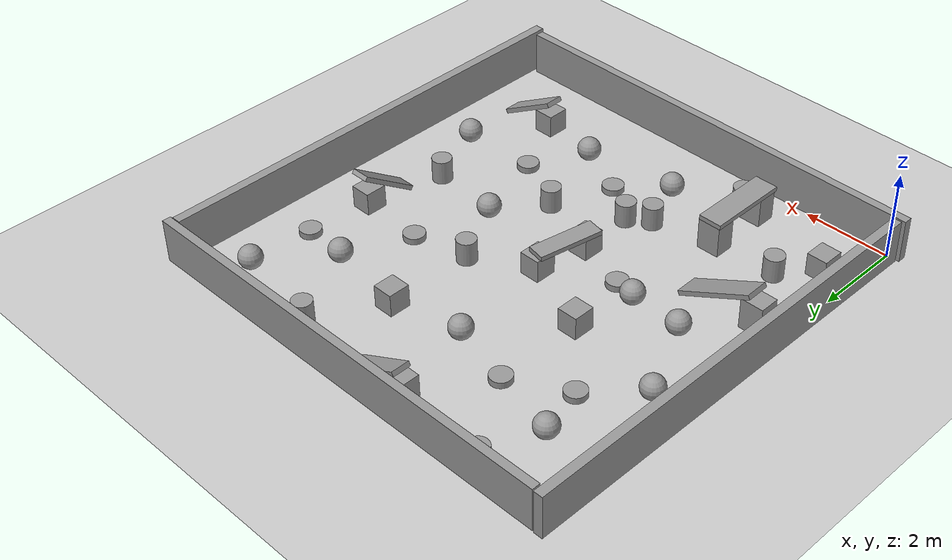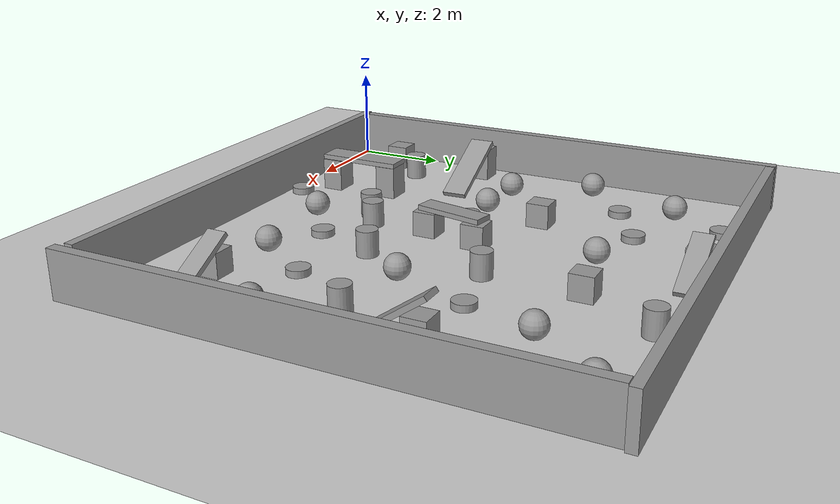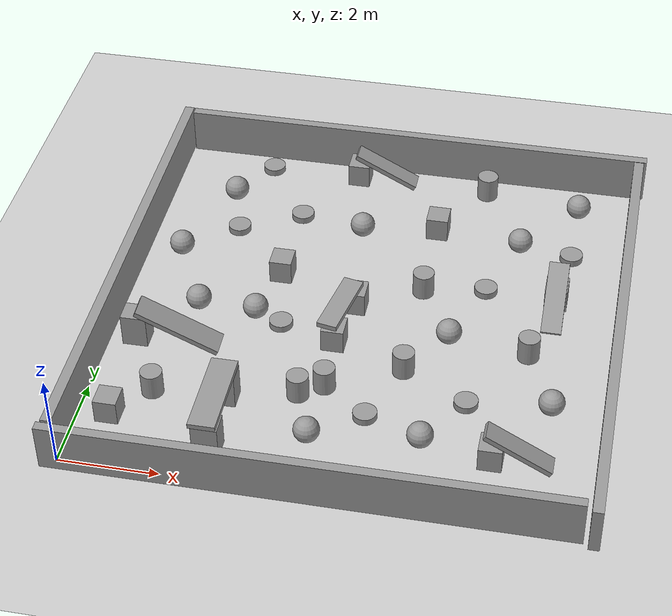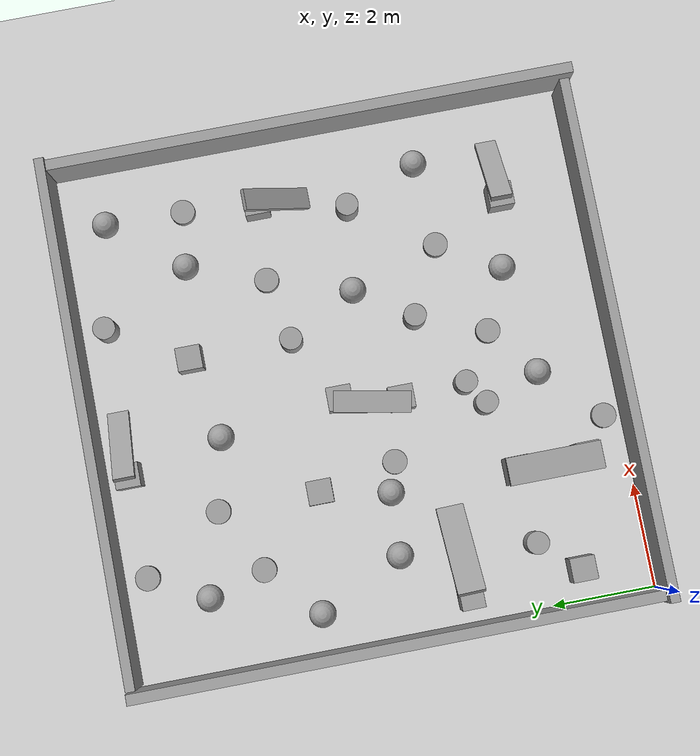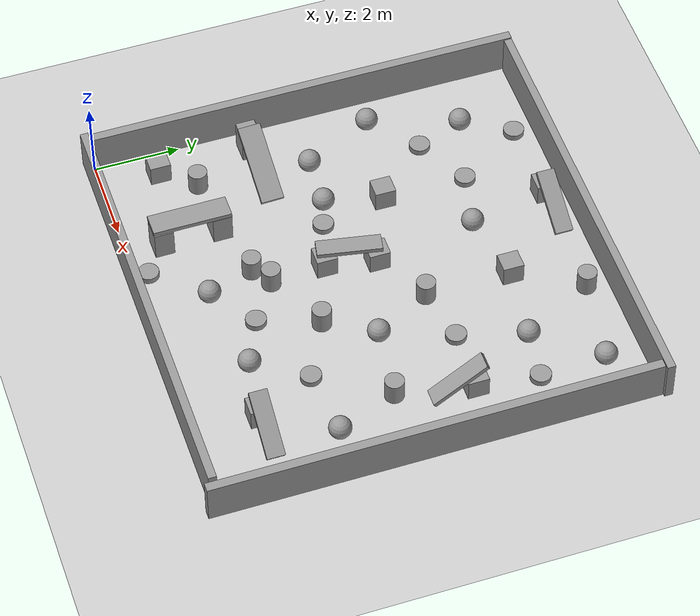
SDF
<sdf version="1.6">
 <world name="default">
  <model name="ground_plane">
   <static>1</static>
   <link name="link">
    <collision name="collision">
     <geometry><plane><normal>0 0 1</normal><size>100 100</size></plane></geometry>
     <surface><friction><ode><mu>100</mu><mu2>50</mu2></ode></friction></surface>
    </collision>
    <visual name="visual">
     <cast_shadows>0</cast_shadows>
     <geometry><plane><normal>0 0 1</normal><size>100 100</size></plane></geometry>
     <material>
      <script><uri>file://media/materials/scripts/gazebo.material</uri><name>Gazebo/Grey</name></script>
     </material>
    </visual>
   </link>
  </model>
  <light name="sun" type="directional">
   <pose>0 0 10 0 -0 0</pose>
   <diffuse>0.8 0.8 0.8 1</diffuse>
   <specular>0.1 0.1 0.1 1</specular>
   <attenuation>
    <range>1000</range>
    <constant>0.9</constant>
    <linear>0.01</linear>
    <quadratic>0.001</quadratic>
   </attenuation>
   <direction>-0.5 0.5 -1</direction>
  </light>
  <gravity>0 0 -9.8</gravity>
  <magnetic_field>6e-06 2.3e-05 -4.2e-05</magnetic_field>
  <atmosphere type="adiabatic"/>
  <physics name="default_physics" default="0" type="ode">
   <max_step_size>0.001</max_step_size>
   <real_time_factor>1</real_time_factor>
   <real_time_update_rate>1000</real_time_update_rate>
  </physics>
  <scene><ambient>0.4 0.4 0.4 1</ambient><background>0.7 0.7 0.7 1</background><shadows>1</shadows></scene>
  <spherical_coordinates>
   <surface_model>EARTH_WGS84</surface_model>
   <latitude_deg>0</latitude_deg>
   <longitude_deg>0</longitude_deg>
   <elevation>0</elevation>
   <heading_deg>0</heading_deg>
  </spherical_coordinates>
  <model name="object1">
   <link name="link">
    <inertial>
     <mass>1</mass>
     <inertia>
      <ixx>0.166667</ixx>
      <ixy>0</ixy>
      <ixz>0</ixz>
      <iyy>0.166667</iyy>
      <iyz>0</iyz>
      <izz>0.166667</izz>
     </inertia>
    </inertial>
    <visual name="visual">
     <geometry><box><size>0.462419 0.484025 0.518106</size></box></geometry>
     <material>
      <script><name>Gazebo/Grey</name><uri>file://media/materials/scripts/gazebo.material</uri></script>
      <ambient>0.3 0.3 0.3 1</ambient>
      <diffuse>0.7 0.7 0.7 1</diffuse>
      <specular>0.01 0.01 0.01 1</specular>
      <emissive>0 0 0 1</emissive>
     </material>
    </visual>
    <collision name="collision">
     <geometry><box><size>0.462419 0.484025 0.518106</size></box></geometry>
     <surface>
      <friction>
       <ode><mu>1</mu><mu2>1</mu2><fdir1>0 0 0</fdir1><slip1>0</slip1><slip2>0</slip2></ode>
       <torsional>
        <coefficient>1</coefficient>
        <patch_radius>0</patch_radius>
        <surface_radius>0</surface_radius>
        <use_patch_radius>1</use_patch_radius>
        <ode><slip>0</slip></ode>
       </torsional>
      </friction>
      <bounce><restitution_coefficient>0</restitution_coefficient><threshold>1e+06</threshold></bounce>
      <contact>
       <collide_without_contact>0</collide_without_contact>
       <collide_without_contact_bitmask>1</collide_without_contact_bitmask>
       <collide_bitmask>1</collide_bitmask>
       <ode>
        <soft_cfm>0</soft_cfm>
        <soft_erp>0.2</soft_erp>
        <kp>1e+13</kp>
        <kd>1</kd>
        <max_vel>0.01</max_vel>
        <min_depth>0</min_depth>
       </ode>
       <bullet>
        <split_impulse>1</split_impulse>
        <split_impulse_penetration_threshold>-0.01</split_impulse_penetration_threshold>
        <soft_cfm>0</soft_cfm>
        <soft_erp>0.2</soft_erp>
        <kp>1e+13</kp>
        <kd>1</kd>
       </bullet>
      </contact>
     </surface>
    </collision>
   </link>
   <static>1</static>
   <pose>0.624317 1.3526 0.259053 0 -0 0</pose>
  </model>
  <model name="object1_clone_0">
   <link name="link">
    <inertial>
     <mass>1</mass>
     <inertia>
      <ixx>0.166667</ixx>
      <ixy>0</ixy>
      <ixz>0</ixz>
      <iyy>0.166667</iyy>
      <iyz>0</iyz>
      <izz>0.166667</izz>
     </inertia>
    </inertial>
    <visual name="visual">
     <geometry><box><size>0.462419 0.484025 0.518106</size></box></geometry>
     <material>
      <script><name>Gazebo/Grey</name><uri>file://media/materials/scripts/gazebo.material</uri></script>
      <ambient>0.3 0.3 0.3 1</ambient>
      <diffuse>0.7 0.7 0.7 1</diffuse>
      <specular>0.01 0.01 0.01 1</specular>
      <emissive>0 0 0 1</emissive>
     </material>
    </visual>
    <collision name="collision">
     <geometry><box><size>0.462419 0.484025 0.518106</size></box></geometry>
     <surface>
      <friction>
       <ode><mu>1</mu><mu2>1</mu2><fdir1>0 0 0</fdir1><slip1>0</slip1><slip2>0</slip2></ode>
       <torsional>
        <coefficient>1</coefficient>
        <patch_radius>0</patch_radius>
        <surface_radius>0</surface_radius>
        <use_patch_radius>1</use_patch_radius>
        <ode><slip>0</slip></ode>
       </torsional>
      </friction>
      <bounce><restitution_coefficient>0</restitution_coefficient><threshold>1e+06</threshold></bounce>
      <contact>
       <collide_without_contact>0</collide_without_contact>
       <collide_without_contact_bitmask>1</collide_without_contact_bitmask>
       <collide_bitmask>1</collide_bitmask>
       <ode>
        <soft_cfm>0</soft_cfm>
        <soft_erp>0.2</soft_erp>
        <kp>1e+13</kp>
        <kd>1</kd>
        <max_vel>0.01</max_vel>
        <min_depth>0</min_depth>
       </ode>
       <bullet>
        <split_impulse>1</split_impulse>
        <split_impulse_penetration_threshold>-0.01</split_impulse_penetration_threshold>
        <soft_cfm>0</soft_cfm>
        <soft_erp>0.2</soft_erp>
        <kp>1e+13</kp>
        <kd>1</kd>
       </bullet>
      </contact>
     </surface>
    </collision>
   </link>
   <static>1</static>
   <pose>4.48758 4.11823 0.259053 0 -0 0</pose>
  </model>
  <model name="object2">
   <link name="link">
    <inertial>
     <mass>1</mass>
     <inertia>
      <ixx>0.166667</ixx>
      <ixy>0</ixy>
      <ixz>0</ixz>
      <iyy>0.166667</iyy>
      <iyz>0</iyz>
      <izz>0.166667</izz>
     </inertia>
    </inertial>
    <visual name="visual">
     <geometry><box><size>0.518422 0.450005 0.707103</size></box></geometry>
     <material>
      <script><name>Gazebo/Grey</name><uri>file://media/materials/scripts/gazebo.material</uri></script>
      <ambient>0.3 0.3 0.3 1</ambient>
      <diffuse>0.7 0.7 0.7 1</diffuse>
      <specular>0.01 0.01 0.01 1</specular>
      <emissive>0 0 0 1</emissive>
     </material>
    </visual>
    <collision name="collision">
     <geometry><box><size>0.518422 0.450005 0.707103</size></box></geometry>
     <surface>
      <friction>
       <ode><mu>1</mu><mu2>1</mu2><fdir1>0 0 0</fdir1><slip1>0</slip1><slip2>0</slip2></ode>
       <torsional>
        <coefficient>1</coefficient>
        <patch_radius>0</patch_radius>
        <surface_radius>0</surface_radius>
        <use_patch_radius>1</use_patch_radius>
        <ode><slip>0</slip></ode>
       </torsional>
      </friction>
      <bounce><restitution_coefficient>0</restitution_coefficient><threshold>1e+06</threshold></bounce>
      <contact>
       <collide_without_contact>0</collide_without_contact>
       <collide_without_contact_bitmask>1</collide_without_contact_bitmask>
       <collide_bitmask>1</collide_bitmask>
       <ode>
        <soft_cfm>0</soft_cfm>
        <soft_erp>0.2</soft_erp>
        <kp>1e+13</kp>
        <kd>1</kd>
        <max_vel>0.01</max_vel>
        <min_depth>0</min_depth>
       </ode>
       <bullet>
        <split_impulse>1</split_impulse>
        <split_impulse_penetration_threshold>-0.01</split_impulse_penetration_threshold>
        <soft_cfm>0</soft_cfm>
        <soft_erp>0.2</soft_erp>
        <kp>1e+13</kp>
        <kd>1</kd>
       </bullet>
      </contact>
     </surface>
    </collision>
   </link>
   <static>1</static>
   <pose>0.547148 3.55385 0.353552 0 -0 0.0094</pose>
  </model>
  <model name="object3">
   <link name="link">
    <inertial>
     <mass>1</mass>
     <inertia>
      <ixx>0.166667</ixx>
      <ixy>0</ixy>
      <ixz>0</ixz>
      <iyy>0.166667</iyy>
      <iyz>0</iyz>
      <izz>0.166667</izz>
     </inertia>
    </inertial>
    <visual name="visual">
     <geometry><box><size>1.83274 0.534759 0.105167</size></box></geometry>
     <material>
      <script><name>Gazebo/Grey</name><uri>file://media/materials/scripts/gazebo.material</uri></script>
      <ambient>0.3 0.3 0.3 1</ambient>
      <diffuse>0.7 0.7 0.7 1</diffuse>
      <specular>0.01 0.01 0.01 1</specular>
      <emissive>0 0 0 1</emissive>
     </material>
    </visual>
    <collision name="collision">
     <geometry><box><size>1.83274 0.534759 0.105167</size></box></geometry>
     <surface>
      <friction>
       <ode><mu>1</mu><mu2>1</mu2><fdir1>0 0 0</fdir1><slip1>0</slip1><slip2>0</slip2></ode>
       <torsional>
        <coefficient>1</coefficient>
        <patch_radius>0</patch_radius>
        <surface_radius>0</surface_radius>
        <use_patch_radius>1</use_patch_radius>
        <ode><slip>0</slip></ode>
       </torsional>
      </friction>
      <bounce><restitution_coefficient>0</restitution_coefficient><threshold>1e+06</threshold></bounce>
      <contact>
       <collide_without_contact>0</collide_without_contact>
       <collide_without_contact_bitmask>1</collide_without_contact_bitmask>
       <collide_bitmask>1</collide_bitmask>
       <ode>
        <soft_cfm>0</soft_cfm>
        <soft_erp>0.2</soft_erp>
        <kp>1e+13</kp>
        <kd>1</kd>
        <max_vel>0.01</max_vel>
        <min_depth>0</min_depth>
       </ode>
       <bullet>
        <split_impulse>1</split_impulse>
        <split_impulse_penetration_threshold>-0.01</split_impulse_penetration_threshold>
        <soft_cfm>0</soft_cfm>
        <soft_erp>0.2</soft_erp>
        <kp>1e+13</kp>
        <kd>1</kd>
       </bullet>
      </contact>
     </surface>
    </collision>
   </link>
   <static>1</static>
   <pose>1.42303 3.57507 0.458088 0.008272 0.462769 0.028019</pose>
  </model>
  <model name="object2_clone">
   <link name="link">
    <inertial>
     <mass>1</mass>
     <inertia>
      <ixx>0.166667</ixx>
      <ixy>0</ixy>
      <ixz>0</ixz>
      <iyy>0.166667</iyy>
      <iyz>0</iyz>
      <izz>0.166667</izz>
     </inertia>
    </inertial>
    <visual name="visual">
     <geometry><box><size>0.518422 0.450005 0.707103</size></box></geometry>
     <material>
      <script><name>Gazebo/Grey</name><uri>file://media/materials/scripts/gazebo.material</uri></script>
      <ambient>0.3 0.3 0.3 1</ambient>
      <diffuse>0.7 0.7 0.7 1</diffuse>
      <specular>0.01 0.01 0.01 1</specular>
      <emissive>0 0 0 1</emissive>
     </material>
    </visual>
    <collision name="collision">
     <geometry><box><size>0.518422 0.450005 0.707103</size></box></geometry>
     <surface>
      <friction>
       <ode><mu>1</mu><mu2>1</mu2><fdir1>0 0 0</fdir1><slip1>0</slip1><slip2>0</slip2></ode>
       <torsional>
        <coefficient>1</coefficient>
        <patch_radius>0</patch_radius>
        <surface_radius>0</surface_radius>
        <use_patch_radius>1</use_patch_radius>
        <ode><slip>0</slip></ode>
       </torsional>
      </friction>
      <bounce><restitution_coefficient>0</restitution_coefficient><threshold>1e+06</threshold></bounce>
      <contact>
       <collide_without_contact>0</collide_without_contact>
       <collide_without_contact_bitmask>1</collide_without_contact_bitmask>
       <collide_bitmask>1</collide_bitmask>
       <ode>
        <soft_cfm>0</soft_cfm>
        <soft_erp>0.2</soft_erp>
        <kp>1e+13</kp>
        <kd>1</kd>
        <max_vel>0.01</max_vel>
        <min_depth>0</min_depth>
       </ode>
       <bullet>
        <split_impulse>1</split_impulse>
        <split_impulse_penetration_threshold>-0.01</split_impulse_penetration_threshold>
        <soft_cfm>0</soft_cfm>
        <soft_erp>0.2</soft_erp>
        <kp>1e+13</kp>
        <kd>1</kd>
       </bullet>
      </contact>
     </surface>
    </collision>
   </link>
   <static>1</static>
   <pose>2.69917 2.20262 0.353552 0 -0 0.0094</pose>
  </model>
  <model name="object2_clone_0">
   <link name="link">
    <inertial>
     <mass>1</mass>
     <inertia>
      <ixx>0.166667</ixx>
      <ixy>0</ixy>
      <ixz>0</ixz>
      <iyy>0.166667</iyy>
      <iyz>0</iyz>
      <izz>0.166667</izz>
     </inertia>
    </inertial>
    <visual name="visual">
     <geometry><box><size>0.518422 0.450005 0.707103</size></box></geometry>
     <material>
      <script><name>Gazebo/Grey</name><uri>file://media/materials/scripts/gazebo.material</uri></script>
      <ambient>0.3 0.3 0.3 1</ambient>
      <diffuse>0.7 0.7 0.7 1</diffuse>
      <specular>0.01 0.01 0.01 1</specular>
      <emissive>0 0 0 1</emissive>
     </material>
    </visual>
    <collision name="collision">
     <geometry><box><size>0.518422 0.450005 0.707103</size></box></geometry>
     <surface>
      <friction>
       <ode><mu>1</mu><mu2>1</mu2><fdir1>0 0 0</fdir1><slip1>0</slip1><slip2>0</slip2></ode>
       <torsional>
        <coefficient>1</coefficient>
        <patch_radius>0</patch_radius>
        <surface_radius>0</surface_radius>
        <use_patch_radius>1</use_patch_radius>
        <ode><slip>0</slip></ode>
       </torsional>
      </friction>
      <bounce><restitution_coefficient>0</restitution_coefficient><threshold>1e+06</threshold></bounce>
      <contact>
       <collide_without_contact>0</collide_without_contact>
       <collide_without_contact_bitmask>1</collide_without_contact_bitmask>
       <collide_bitmask>1</collide_bitmask>
       <ode>
        <soft_cfm>0</soft_cfm>
        <soft_erp>0.2</soft_erp>
        <kp>1e+13</kp>
        <kd>1</kd>
        <max_vel>0.01</max_vel>
        <min_depth>0</min_depth>
       </ode>
       <bullet>
        <split_impulse>1</split_impulse>
        <split_impulse_penetration_threshold>-0.01</split_impulse_penetration_threshold>
        <soft_cfm>0</soft_cfm>
        <soft_erp>0.2</soft_erp>
        <kp>1e+13</kp>
        <kd>1</kd>
       </bullet>
      </contact>
     </surface>
    </collision>
   </link>
   <static>1</static>
   <pose>2.7204 0.828022 0.353552 0 -0 0.0094</pose>
  </model>
  <model name="object3_clone">
   <link name="link">
    <inertial>
     <mass>1</mass>
     <inertia>
      <ixx>0.166667</ixx>
      <ixy>0</ixy>
      <ixz>0</ixz>
      <iyy>0.166667</iyy>
      <iyz>0</iyz>
      <izz>0.166667</izz>
     </inertia>
    </inertial>
    <visual name="visual">
     <geometry><box><size>1.83274 0.534759 0.105167</size></box></geometry>
     <material>
      <script><name>Gazebo/Grey</name><uri>file://media/materials/scripts/gazebo.material</uri></script>
      <ambient>0.3 0.3 0.3 1</ambient>
      <diffuse>0.7 0.7 0.7 1</diffuse>
      <specular>0.01 0.01 0.01 1</specular>
      <emissive>0 0 0 1</emissive>
     </material>
    </visual>
    <collision name="collision">
     <geometry><box><size>1.83274 0.534759 0.105167</size></box></geometry>
     <surface>
      <friction>
       <ode><mu>1</mu><mu2>1</mu2><fdir1>0 0 0</fdir1><slip1>0</slip1><slip2>0</slip2></ode>
       <torsional>
        <coefficient>1</coefficient>
        <patch_radius>0</patch_radius>
        <surface_radius>0</surface_radius>
        <use_patch_radius>1</use_patch_radius>
        <ode><slip>0</slip></ode>
       </torsional>
      </friction>
      <bounce><restitution_coefficient>0</restitution_coefficient><threshold>1e+06</threshold></bounce>
      <contact>
       <collide_without_contact>0</collide_without_contact>
       <collide_without_contact_bitmask>1</collide_without_contact_bitmask>
       <collide_bitmask>1</collide_bitmask>
       <ode>
        <soft_cfm>0</soft_cfm>
        <soft_erp>0.2</soft_erp>
        <kp>1e+13</kp>
        <kd>1</kd>
        <max_vel>0.01</max_vel>
        <min_depth>0</min_depth>
       </ode>
       <bullet>
        <split_impulse>1</split_impulse>
        <split_impulse_penetration_threshold>-0.01</split_impulse_penetration_threshold>
        <soft_cfm>0</soft_cfm>
        <soft_erp>0.2</soft_erp>
        <kp>1e+13</kp>
        <kd>1</kd>
       </bullet>
      </contact>
     </surface>
    </collision>
   </link>
   <static>1</static>
   <pose>2.6845 1.51565 0.75991 0 0 -1.57</pose>
  </model>
  <model name="object4">
   <link name="link">
    <inertial>
     <mass>1</mass>
     <inertia><ixx>0.1</ixx><ixy>0</ixy><ixz>0</ixz><iyy>0.1</iyy><iyz>0</iyz><izz>0.1</izz></inertia>
    </inertial>
    <visual name="visual">
     <geometry><sphere><radius>0.260368</radius></sphere></geometry>
     <material>
      <script><name>Gazebo/Grey</name><uri>file://media/materials/scripts/gazebo.material</uri></script>
      <ambient>0.3 0.3 0.3 1</ambient>
      <diffuse>0.7 0.7 0.7 1</diffuse>
      <specular>0.01 0.01 0.01 1</specular>
      <emissive>0 0 0 1</emissive>
     </material>
    </visual>
    <collision name="collision">
     <geometry><sphere><radius>0.260368</radius></sphere></geometry>
     <surface>
      <friction>
       <ode><mu>1</mu><mu2>1</mu2><fdir1>0 0 0</fdir1><slip1>0</slip1><slip2>0</slip2></ode>
       <torsional>
        <coefficient>1</coefficient>
        <patch_radius>0</patch_radius>
        <surface_radius>0</surface_radius>
        <use_patch_radius>1</use_patch_radius>
        <ode><slip>0</slip></ode>
       </torsional>
      </friction>
      <bounce><restitution_coefficient>0</restitution_coefficient><threshold>1e+06</threshold></bounce>
      <contact>
       <collide_without_contact>0</collide_without_contact>
       <collide_without_contact_bitmask>1</collide_without_contact_bitmask>
       <collide_bitmask>1</collide_bitmask>
       <ode>
        <soft_cfm>0</soft_cfm>
        <soft_erp>0.2</soft_erp>
        <kp>1e+13</kp>
        <kd>1</kd>
        <max_vel>0.01</max_vel>
        <min_depth>0</min_depth>
       </ode>
       <bullet>
        <split_impulse>1</split_impulse>
        <split_impulse_penetration_threshold>-0.01</split_impulse_penetration_threshold>
        <soft_cfm>0</soft_cfm>
        <soft_erp>0.2</soft_erp>
        <kp>1e+13</kp>
        <kd>1</kd>
       </bullet>
      </contact>
     </surface>
    </collision>
   </link>
   <static>1</static>
   <pose>4.4994 1.41888 0.247825 0 -0 0</pose>
  </model>
  <model name="object4_clone">
   <link name="link">
    <inertial>
     <mass>1</mass>
     <inertia><ixx>0.1</ixx><ixy>0</ixy><ixz>0</ixz><iyy>0.1</iyy><iyz>0</iyz><izz>0.1</izz></inertia>
    </inertial>
    <visual name="visual">
     <geometry><sphere><radius>0.260368</radius></sphere></geometry>
     <material>
      <script><name>Gazebo/Grey</name><uri>file://media/materials/scripts/gazebo.material</uri></script>
      <ambient>0.3 0.3 0.3 1</ambient>
      <diffuse>0.7 0.7 0.7 1</diffuse>
      <specular>0.01 0.01 0.01 1</specular>
      <emissive>0 0 0 1</emissive>
     </material>
    </visual>
    <collision name="collision">
     <geometry><sphere><radius>0.260368</radius></sphere></geometry>
     <surface>
      <friction>
       <ode><mu>1</mu><mu2>1</mu2><fdir1>0 0 0</fdir1><slip1>0</slip1><slip2>0</slip2></ode>
       <torsional>
        <coefficient>1</coefficient>
        <patch_radius>0</patch_radius>
        <surface_radius>0</surface_radius>
        <use_patch_radius>1</use_patch_radius>
        <ode><slip>0</slip></ode>
       </torsional>
      </friction>
      <bounce><restitution_coefficient>0</restitution_coefficient><threshold>1e+06</threshold></bounce>
      <contact>
       <collide_without_contact>0</collide_without_contact>
       <collide_without_contact_bitmask>1</collide_without_contact_bitmask>
       <collide_bitmask>1</collide_bitmask>
       <ode>
        <soft_cfm>0</soft_cfm>
        <soft_erp>0.2</soft_erp>
        <kp>1e+13</kp>
        <kd>1</kd>
        <max_vel>0.01</max_vel>
        <min_depth>0</min_depth>
       </ode>
       <bullet>
        <split_impulse>1</split_impulse>
        <split_impulse_penetration_threshold>-0.01</split_impulse_penetration_threshold>
        <soft_cfm>0</soft_cfm>
        <soft_erp>0.2</soft_erp>
        <kp>1e+13</kp>
        <kd>1</kd>
       </bullet>
      </contact>
     </surface>
    </collision>
   </link>
   <static>1</static>
   <pose>2.73638 4.65874 0.260368 0 -0 0</pose>
  </model>
  <model name="object4_clone_0">
   <link name="link">
    <inertial>
     <mass>1</mass>
     <inertia><ixx>0.1</ixx><ixy>0</ixy><ixz>0</ixz><iyy>0.1</iyy><iyz>0</iyz><izz>0.1</izz></inertia>
    </inertial>
    <visual name="visual">
     <geometry><sphere><radius>0.260368</radius></sphere></geometry>
     <material>
      <script><name>Gazebo/Grey</name><uri>file://media/materials/scripts/gazebo.material</uri></script>
      <ambient>0.3 0.3 0.3 1</ambient>
      <diffuse>0.7 0.7 0.7 1</diffuse>
      <specular>0.01 0.01 0.01 1</specular>
      <emissive>0 0 0 1</emissive>
     </material>
    </visual>
    <collision name="collision">
     <geometry><sphere><radius>0.260368</radius></sphere></geometry>
     <surface>
      <friction>
       <ode><mu>1</mu><mu2>1</mu2><fdir1>0 0 0</fdir1><slip1>0</slip1><slip2>0</slip2></ode>
       <torsional>
        <coefficient>1</coefficient>
        <patch_radius>0</patch_radius>
        <surface_radius>0</surface_radius>
        <use_patch_radius>1</use_patch_radius>
        <ode><slip>0</slip></ode>
       </torsional>
      </friction>
      <bounce><restitution_coefficient>0</restitution_coefficient><threshold>1e+06</threshold></bounce>
      <contact>
       <collide_without_contact>0</collide_without_contact>
       <collide_without_contact_bitmask>1</collide_without_contact_bitmask>
       <collide_bitmask>1</collide_bitmask>
       <ode>
        <soft_cfm>0</soft_cfm>
        <soft_erp>0.2</soft_erp>
        <kp>1e+13</kp>
        <kd>1</kd>
        <max_vel>0.01</max_vel>
        <min_depth>0</min_depth>
       </ode>
       <bullet>
        <split_impulse>1</split_impulse>
        <split_impulse_penetration_threshold>-0.01</split_impulse_penetration_threshold>
        <soft_cfm>0</soft_cfm>
        <soft_erp>0.2</soft_erp>
        <kp>1e+13</kp>
        <kd>1</kd>
       </bullet>
      </contact>
     </surface>
    </collision>
   </link>
   <static>1</static>
   <pose>1.5218 4.71849 0.260368 0 -0 0</pose>
  </model>
  <model name="object5">
   <link name="link">
    <inertial>
     <mass>1</mass>
     <inertia><ixx>0.145833</ixx><ixy>0</ixy><ixz>0</ixz><iyy>0.145833</iyy><iyz>0</iyz><izz>0.125</izz></inertia>
    </inertial>
    <visual name="visual">
     <geometry><cylinder><radius>0.221555</radius><length>0.542695</length></cylinder></geometry>
     <material>
      <script><name>Gazebo/Grey</name><uri>file://media/materials/scripts/gazebo.material</uri></script>
      <ambient>0.3 0.3 0.3 1</ambient>
      <diffuse>0.7 0.7 0.7 1</diffuse>
      <specular>0.01 0.01 0.01 1</specular>
      <emissive>0 0 0 1</emissive>
     </material>
    </visual>
    <collision name="collision">
     <geometry><cylinder><radius>0.221555</radius><length>0.542695</length></cylinder></geometry>
     <surface>
      <friction>
       <ode><mu>1</mu><mu2>1</mu2><fdir1>0 0 0</fdir1><slip1>0</slip1><slip2>0</slip2></ode>
       <torsional>
        <coefficient>1</coefficient>
        <patch_radius>0</patch_radius>
        <surface_radius>0</surface_radius>
        <use_patch_radius>1</use_patch_radius>
        <ode><slip>0</slip></ode>
       </torsional>
      </friction>
      <bounce><restitution_coefficient>0</restitution_coefficient><threshold>1e+06</threshold></bounce>
      <contact>
       <collide_without_contact>0</collide_without_contact>
       <collide_without_contact_bitmask>1</collide_without_contact_bitmask>
       <collide_bitmask>1</collide_bitmask>
       <ode>
        <soft_cfm>0</soft_cfm>
        <soft_erp>0.2</soft_erp>
        <kp>1e+13</kp>
        <kd>1</kd>
        <max_vel>0.01</max_vel>
        <min_depth>0</min_depth>
       </ode>
       <bullet>
        <split_impulse>1</split_impulse>
        <split_impulse_penetration_threshold>-0.01</split_impulse_penetration_threshold>
        <soft_cfm>0</soft_cfm>
        <soft_erp>0.2</soft_erp>
        <kp>1e+13</kp>
        <kd>1</kd>
       </bullet>
      </contact>
     </surface>
    </collision>
   </link>
   <static>1</static>
   <pose>1.26811 2.11132 0.271347 0 -0 0</pose>
  </model>
  <model name="object5_clone">
   <link name="link">
    <inertial>
     <mass>1</mass>
     <inertia><ixx>0.145833</ixx><ixy>0</ixy><ixz>0</ixz><iyy>0.145833</iyy><iyz>0</iyz><izz>0.125</izz></inertia>
    </inertial>
    <visual name="visual">
     <geometry><cylinder><radius>0.221555</radius><length>0.542695</length></cylinder></geometry>
     <material>
      <script><name>Gazebo/Grey</name><uri>file://media/materials/scripts/gazebo.material</uri></script>
      <ambient>0.3 0.3 0.3 1</ambient>
      <diffuse>0.7 0.7 0.7 1</diffuse>
      <specular>0.01 0.01 0.01 1</specular>
      <emissive>0 0 0 1</emissive>
     </material>
    </visual>
    <collision name="collision">
     <geometry><cylinder><radius>0.221555</radius><length>0.542695</length></cylinder></geometry>
     <surface>
      <friction>
       <ode><mu>1</mu><mu2>1</mu2><fdir1>0 0 0</fdir1><slip1>0</slip1><slip2>0</slip2></ode>
       <torsional>
        <coefficient>1</coefficient>
        <patch_radius>0</patch_radius>
        <surface_radius>0</surface_radius>
        <use_patch_radius>1</use_patch_radius>
        <ode><slip>0</slip></ode>
       </torsional>
      </friction>
      <bounce><restitution_coefficient>0</restitution_coefficient><threshold>1e+06</threshold></bounce>
      <contact>
       <collide_without_contact>0</collide_without_contact>
       <collide_without_contact_bitmask>1</collide_without_contact_bitmask>
       <collide_bitmask>1</collide_bitmask>
       <ode>
        <soft_cfm>0</soft_cfm>
        <soft_erp>0.2</soft_erp>
        <kp>1e+13</kp>
        <kd>1</kd>
        <max_vel>0.01</max_vel>
        <min_depth>0</min_depth>
       </ode>
       <bullet>
        <split_impulse>1</split_impulse>
        <split_impulse_penetration_threshold>-0.01</split_impulse_penetration_threshold>
        <soft_cfm>0</soft_cfm>
        <soft_erp>0.2</soft_erp>
        <kp>1e+13</kp>
        <kd>1</kd>
       </bullet>
      </contact>
     </surface>
    </collision>
   </link>
   <static>1</static>
   <pose>4.08789 2.52624 0.271347 0 -0 0</pose>
  </model>
  <model name="object5_clone_0">
   <link name="link">
    <inertial>
     <mass>1</mass>
     <inertia><ixx>0.145833</ixx><ixy>0</ixy><ixz>0</ixz><iyy>0.145833</iyy><iyz>0</iyz><izz>0.125</izz></inertia>
    </inertial>
    <visual name="visual">
     <geometry><cylinder><radius>0.221555</radius><length>0.542695</length></cylinder></geometry>
     <material>
      <script><name>Gazebo/Grey</name><uri>file://media/materials/scripts/gazebo.material</uri></script>
      <ambient>0.3 0.3 0.3 1</ambient>
      <diffuse>0.7 0.7 0.7 1</diffuse>
      <specular>0.01 0.01 0.01 1</specular>
      <emissive>0 0 0 1</emissive>
     </material>
    </visual>
    <collision name="collision">
     <geometry><cylinder><radius>0.221555</radius><length>0.542695</length></cylinder></geometry>
     <surface>
      <friction>
       <ode><mu>1</mu><mu2>1</mu2><fdir1>0 0 0</fdir1><slip1>0</slip1><slip2>0</slip2></ode>
       <torsional>
        <coefficient>1</coefficient>
        <patch_radius>0</patch_radius>
        <surface_radius>0</surface_radius>
        <use_patch_radius>1</use_patch_radius>
        <ode><slip>0</slip></ode>
       </torsional>
      </friction>
      <bounce><restitution_coefficient>0</restitution_coefficient><threshold>1e+06</threshold></bounce>
      <contact>
       <collide_without_contact>0</collide_without_contact>
       <collide_without_contact_bitmask>1</collide_without_contact_bitmask>
       <collide_bitmask>1</collide_bitmask>
       <ode>
        <soft_cfm>0</soft_cfm>
        <soft_erp>0.2</soft_erp>
        <kp>1e+13</kp>
        <kd>1</kd>
        <max_vel>0.01</max_vel>
        <min_depth>0</min_depth>
       </ode>
       <bullet>
        <split_impulse>1</split_impulse>
        <split_impulse_penetration_threshold>-0.01</split_impulse_penetration_threshold>
        <soft_cfm>0</soft_cfm>
        <soft_erp>0.2</soft_erp>
        <kp>1e+13</kp>
        <kd>1</kd>
       </bullet>
      </contact>
     </surface>
    </collision>
   </link>
   <static>1</static>
   <pose>4.55176 2.83976 0.271347 0 -0 0</pose>
  </model>
  <model name="object6">
   <link name="link">
    <inertial>
     <mass>1</mass>
     <inertia><ixx>0.145833</ixx><ixy>0</ixy><ixz>0</ixz><iyy>0.145833</iyy><iyz>0</iyz><izz>0.125</izz></inertia>
    </inertial>
    <visual name="visual">
     <geometry><cylinder><radius>0.240804</radius><length>0.144464</length></cylinder></geometry>
     <material>
      <script><name>Gazebo/Grey</name><uri>file://media/materials/scripts/gazebo.material</uri></script>
      <ambient>0.3 0.3 0.3 1</ambient>
      <diffuse>0.7 0.7 0.7 1</diffuse>
      <specular>0.01 0.01 0.01 1</specular>
      <emissive>0 0 0 1</emissive>
     </material>
    </visual>
    <collision name="collision">
     <geometry><cylinder><radius>0.240804</radius><length>0.144464</length></cylinder></geometry>
     <surface>
      <friction>
       <ode><mu>1</mu><mu2>1</mu2><fdir1>0 0 0</fdir1><slip1>0</slip1><slip2>0</slip2></ode>
       <torsional>
        <coefficient>1</coefficient>
        <patch_radius>0</patch_radius>
        <surface_radius>0</surface_radius>
        <use_patch_radius>1</use_patch_radius>
        <ode><slip>0</slip></ode>
       </torsional>
      </friction>
      <bounce><restitution_coefficient>0</restitution_coefficient><threshold>1e+06</threshold></bounce>
      <contact>
       <collide_without_contact>0</collide_without_contact>
       <collide_without_contact_bitmask>1</collide_without_contact_bitmask>
       <collide_bitmask>1</collide_bitmask>
       <ode>
        <soft_cfm>0</soft_cfm>
        <soft_erp>0.2</soft_erp>
        <kp>1e+13</kp>
        <kd>1</kd>
        <max_vel>0.01</max_vel>
        <min_depth>0</min_depth>
       </ode>
       <bullet>
        <split_impulse>1</split_impulse>
        <split_impulse_penetration_threshold>-0.01</split_impulse_penetration_threshold>
        <soft_cfm>0</soft_cfm>
        <soft_erp>0.2</soft_erp>
        <kp>1e+13</kp>
        <kd>1</kd>
       </bullet>
      </contact>
     </surface>
    </collision>
   </link>
   <static>1</static>
   <pose>3.30642 4.4703 0.072232 0 -0 0</pose>
  </model>
  <model name="object6_clone">
   <link name="link">
    <inertial>
     <mass>1</mass>
     <inertia><ixx>0.145833</ixx><ixy>0</ixy><ixz>0</ixz><iyy>0.145833</iyy><iyz>0</iyz><izz>0.125</izz></inertia>
    </inertial>
    <visual name="visual">
     <geometry><cylinder><radius>0.240804</radius><length>0.144464</length></cylinder></geometry>
     <material>
      <script><name>Gazebo/Grey</name><uri>file://media/materials/scripts/gazebo.material</uri></script>
      <ambient>0.3 0.3 0.3 1</ambient>
      <diffuse>0.7 0.7 0.7 1</diffuse>
      <specular>0.01 0.01 0.01 1</specular>
      <emissive>0 0 0 1</emissive>
     </material>
    </visual>
    <collision name="collision">
     <geometry><cylinder><radius>0.240804</radius><length>0.144464</length></cylinder></geometry>
     <surface>
      <friction>
       <ode><mu>1</mu><mu2>1</mu2><fdir1>0 0 0</fdir1><slip1>0</slip1><slip2>0</slip2></ode>
       <torsional>
        <coefficient>1</coefficient>
        <patch_radius>0</patch_radius>
        <surface_radius>0</surface_radius>
        <use_patch_radius>1</use_patch_radius>
        <ode><slip>0</slip></ode>
       </torsional>
      </friction>
      <bounce><restitution_coefficient>0</restitution_coefficient><threshold>1e+06</threshold></bounce>
      <contact>
       <collide_without_contact>0</collide_without_contact>
       <collide_without_contact_bitmask>1</collide_without_contact_bitmask>
       <collide_bitmask>1</collide_bitmask>
       <ode>
        <soft_cfm>0</soft_cfm>
        <soft_erp>0.2</soft_erp>
        <kp>1e+13</kp>
        <kd>1</kd>
        <max_vel>0.01</max_vel>
        <min_depth>0</min_depth>
       </ode>
       <bullet>
        <split_impulse>1</split_impulse>
        <split_impulse_penetration_threshold>-0.01</split_impulse_penetration_threshold>
        <soft_cfm>0</soft_cfm>
        <soft_erp>0.2</soft_erp>
        <kp>1e+13</kp>
        <kd>1</kd>
       </bullet>
      </contact>
     </surface>
    </collision>
   </link>
   <static>1</static>
   <pose>3.42647 0.307172 0.072232 0 -0 0</pose>
  </model>
  <model name="wall2">
   <link name="link">
    <inertial>
     <mass>1</mass>
     <inertia>
      <ixx>0.166667</ixx>
      <ixy>0</ixy>
      <ixz>0</ixz>
      <iyy>0.166667</iyy>
      <iyz>0</iyz>
      <izz>0.166667</izz>
     </inertia>
    </inertial>
    <visual name="visual">
     <geometry><box><size>0.209732 10.1924 1</size></box></geometry>
     <material>
      <script><name>Gazebo/Grey</name><uri>file://media/materials/scripts/gazebo.material</uri></script>
      <ambient>0.3 0.3 0.3 1</ambient>
      <diffuse>0.7 0.7 0.7 1</diffuse>
      <specular>0.01 0.01 0.01 1</specular>
      <emissive>0 0 0 1</emissive>
     </material>
    </visual>
    <collision name="collision">
     <geometry><box><size>0.209732 10.1924 1</size></box></geometry>
     <surface>
      <friction>
       <ode><mu>1</mu><mu2>1</mu2><fdir1>0 0 0</fdir1><slip1>0</slip1><slip2>0</slip2></ode>
       <torsional>
        <coefficient>1</coefficient>
        <patch_radius>0</patch_radius>
        <surface_radius>0</surface_radius>
        <use_patch_radius>1</use_patch_radius>
        <ode><slip>0</slip></ode>
       </torsional>
      </friction>
      <bounce><restitution_coefficient>0</restitution_coefficient><threshold>1e+06</threshold></bounce>
      <contact>
       <collide_without_contact>0</collide_without_contact>
       <collide_without_contact_bitmask>1</collide_without_contact_bitmask>
       <collide_bitmask>1</collide_bitmask>
       <ode>
        <soft_cfm>0</soft_cfm>
        <soft_erp>0.2</soft_erp>
        <kp>1e+13</kp>
        <kd>1</kd>
        <max_vel>0.01</max_vel>
        <min_depth>0</min_depth>
       </ode>
       <bullet>
        <split_impulse>1</split_impulse>
        <split_impulse_penetration_threshold>-0.01</split_impulse_penetration_threshold>
        <soft_cfm>0</soft_cfm>
        <soft_erp>0.2</soft_erp>
        <kp>1e+13</kp>
        <kd>1</kd>
       </bullet>
      </contact>
     </surface>
    </collision>
   </link>
   <static>1</static>
   <pose>-0.109062 5.11991 0.5 0 -0 0</pose>
  </model>
  <model name="wall2_clone">
   <link name="link">
    <inertial>
     <mass>1</mass>
     <inertia>
      <ixx>0.166667</ixx>
      <ixy>0</ixy>
      <ixz>0</ixz>
      <iyy>0.166667</iyy>
      <iyz>0</iyz>
      <izz>0.166667</izz>
     </inertia>
    </inertial>
    <visual name="visual">
     <geometry><box><size>0.209732 10.3294 1</size></box></geometry>
     <material>
      <script><name>Gazebo/Grey</name><uri>file://media/materials/scripts/gazebo.material</uri></script>
      <ambient>0.3 0.3 0.3 1</ambient>
      <diffuse>0.7 0.7 0.7 1</diffuse>
      <specular>0.01 0.01 0.01 1</specular>
      <emissive>0 0 0 1</emissive>
     </material>
    </visual>
    <collision name="collision">
     <geometry><box><size>0.209732 10.3294 1</size></box></geometry>
     <surface>
      <friction>
       <ode><mu>1</mu><mu2>1</mu2><fdir1>0 0 0</fdir1><slip1>0</slip1><slip2>0</slip2></ode>
       <torsional>
        <coefficient>1</coefficient>
        <patch_radius>0</patch_radius>
        <surface_radius>0</surface_radius>
        <use_patch_radius>1</use_patch_radius>
        <ode><slip>0</slip></ode>
       </torsional>
      </friction>
      <bounce><restitution_coefficient>0</restitution_coefficient><threshold>1e+06</threshold></bounce>
      <contact>
       <collide_without_contact>0</collide_without_contact>
       <collide_without_contact_bitmask>1</collide_without_contact_bitmask>
       <collide_bitmask>1</collide_bitmask>
       <ode>
        <soft_cfm>0</soft_cfm>
        <soft_erp>0.2</soft_erp>
        <kp>1e+13</kp>
        <kd>1</kd>
        <max_vel>0.01</max_vel>
        <min_depth>0</min_depth>
       </ode>
       <bullet>
        <split_impulse>1</split_impulse>
        <split_impulse_penetration_threshold>-0.01</split_impulse_penetration_threshold>
        <soft_cfm>0</soft_cfm>
        <soft_erp>0.2</soft_erp>
        <kp>1e+13</kp>
        <kd>1</kd>
       </bullet>
      </contact>
     </surface>
    </collision>
   </link>
   <static>1</static>
   <pose>10.1152 4.83597 0.5 0 -0 0</pose>
  </model>
  <model name="wall1_0">
   <link name="link">
    <inertial>
     <mass>1</mass>
     <inertia>
      <ixx>0.166667</ixx>
      <ixy>0</ixy>
      <ixz>0</ixz>
      <iyy>0.166667</iyy>
      <iyz>0</iyz>
      <izz>0.166667</izz>
     </inertia>
    </inertial>
    <visual name="visual">
     <geometry><box><size>10.251 0.189922 1</size></box></geometry>
     <material>
      <script><name>Gazebo/Grey</name><uri>file://media/materials/scripts/gazebo.material</uri></script>
      <ambient>0.3 0.3 0.3 1</ambient>
      <diffuse>0.7 0.7 0.7 1</diffuse>
      <specular>0.01 0.01 0.01 1</specular>
      <emissive>0 0 0 1</emissive>
     </material>
    </visual>
    <collision name="collision">
     <geometry><box><size>10.251 0.189922 1</size></box></geometry>
     <surface>
      <friction>
       <ode><mu>1</mu><mu2>1</mu2><fdir1>0 0 0</fdir1><slip1>0</slip1><slip2>0</slip2></ode>
       <torsional>
        <coefficient>1</coefficient>
        <patch_radius>0</patch_radius>
        <surface_radius>0</surface_radius>
        <use_patch_radius>1</use_patch_radius>
        <ode><slip>0</slip></ode>
       </torsional>
      </friction>
      <bounce><restitution_coefficient>0</restitution_coefficient><threshold>1e+06</threshold></bounce>
      <contact>
       <collide_without_contact>0</collide_without_contact>
       <collide_without_contact_bitmask>1</collide_without_contact_bitmask>
       <collide_bitmask>1</collide_bitmask>
       <ode>
        <soft_cfm>0</soft_cfm>
        <soft_erp>0.2</soft_erp>
        <kp>1e+13</kp>
        <kd>1</kd>
        <max_vel>0.01</max_vel>
        <min_depth>0</min_depth>
       </ode>
       <bullet>
        <split_impulse>1</split_impulse>
        <split_impulse_penetration_threshold>-0.01</split_impulse_penetration_threshold>
        <soft_cfm>0</soft_cfm>
        <soft_erp>0.2</soft_erp>
        <kp>1e+13</kp>
        <kd>1</kd>
       </bullet>
      </contact>
     </surface>
    </collision>
   </link>
   <static>1</static>
   <pose>5.153 10.11 0.5 0 -0 0</pose>
  </model>
  <model name="wall1_0_clone">
   <link name="link">
    <inertial>
     <mass>1</mass>
     <inertia>
      <ixx>0.166667</ixx>
      <ixy>0</ixy>
      <ixz>0</ixz>
      <iyy>0.166667</iyy>
      <iyz>0</iyz>
      <izz>0.166667</izz>
     </inertia>
    </inertial>
    <visual name="visual">
     <geometry><box><size>10.1915 0.189922 1</size></box></geometry>
     <material>
      <script><name>Gazebo/Grey</name><uri>file://media/materials/scripts/gazebo.material</uri></script>
      <ambient>0.3 0.3 0.3 1</ambient>
      <diffuse>0.7 0.7 0.7 1</diffuse>
      <specular>0.01 0.01 0.01 1</specular>
      <emissive>0 0 0 1</emissive>
     </material>
    </visual>
    <collision name="collision">
     <geometry><box><size>10.1915 0.189922 1</size></box></geometry>
     <surface>
      <friction>
       <ode><mu>1</mu><mu2>1</mu2><fdir1>0 0 0</fdir1><slip1>0</slip1><slip2>0</slip2></ode>
       <torsional>
        <coefficient>1</coefficient>
        <patch_radius>0</patch_radius>
        <surface_radius>0</surface_radius>
        <use_patch_radius>1</use_patch_radius>
        <ode><slip>0</slip></ode>
       </torsional>
      </friction>
      <bounce><restitution_coefficient>0</restitution_coefficient><threshold>1e+06</threshold></bounce>
      <contact>
       <collide_without_contact>0</collide_without_contact>
       <collide_without_contact_bitmask>1</collide_without_contact_bitmask>
       <collide_bitmask>1</collide_bitmask>
       <ode>
        <soft_cfm>0</soft_cfm>
        <soft_erp>0.2</soft_erp>
        <kp>1e+13</kp>
        <kd>1</kd>
        <max_vel>0.01</max_vel>
        <min_depth>0</min_depth>
       </ode>
       <bullet>
        <split_impulse>1</split_impulse>
        <split_impulse_penetration_threshold>-0.01</split_impulse_penetration_threshold>
        <soft_cfm>0</soft_cfm>
        <soft_erp>0.2</soft_erp>
        <kp>1e+13</kp>
        <kd>1</kd>
       </bullet>
      </contact>
     </surface>
    </collision>
   </link>
   <static>1</static>
   <pose>4.82102 -0.119292 0.5 0 -0 0</pose>
  </model>
  <audio><device>default</device></audio>
  <model name="object4_clone_1">
   <link name="link">
    <inertial>
     <mass>1</mass>
     <inertia><ixx>0.1</ixx><ixy>0</ixy><ixz>0</ixz><iyy>0.1</iyy><iyz>0</iyz><izz>0.1</izz></inertia>
    </inertial>
    <visual name="visual">
     <geometry><sphere><radius>0.260368</radius></sphere></geometry>
     <material>
      <script><name>Gazebo/Grey</name><uri>file://media/materials/scripts/gazebo.material</uri></script>
      <ambient>0.3 0.3 0.3 1</ambient>
      <diffuse>0.7 0.7 0.7 1</diffuse>
      <specular>0.01 0.01 0.01 1</specular>
      <emissive>0 0 0 1</emissive>
     </material>
    </visual>
    <collision name="collision">
     <geometry><sphere><radius>0.260368</radius></sphere></geometry>
     <surface>
      <friction>
       <ode><mu>1</mu><mu2>1</mu2><fdir1>0 0 0</fdir1><slip1>0</slip1><slip2>0</slip2></ode>
       <torsional>
        <coefficient>1</coefficient>
        <patch_radius>0</patch_radius>
        <surface_radius>0</surface_radius>
        <use_patch_radius>1</use_patch_radius>
        <ode><slip>0</slip></ode>
       </torsional>
      </friction>
      <bounce><restitution_coefficient>0</restitution_coefficient><threshold>1e+06</threshold></bounce>
      <contact>
       <collide_without_contact>0</collide_without_contact>
       <collide_without_contact_bitmask>1</collide_without_contact_bitmask>
       <collide_bitmask>1</collide_bitmask>
       <ode>
        <soft_cfm>0</soft_cfm>
        <soft_erp>0.2</soft_erp>
        <kp>1e+13</kp>
        <kd>1</kd>
        <max_vel>0.01</max_vel>
        <min_depth>0</min_depth>
       </ode>
       <bullet>
        <split_impulse>1</split_impulse>
        <split_impulse_penetration_threshold>-0.01</split_impulse_penetration_threshold>
        <soft_cfm>0</soft_cfm>
        <soft_erp>0.2</soft_erp>
        <kp>1e+13</kp>
        <kd>1</kd>
       </bullet>
      </contact>
     </surface>
    </collision>
   </link>
   <static>1</static>
   <pose>6.64159 1.68671 0.247825 0 -0 0</pose>
  </model>
  <model name="object4_clone_2">
   <link name="link">
    <inertial>
     <mass>1</mass>
     <inertia><ixx>0.1</ixx><ixy>0</ixy><ixz>0</ixz><iyy>0.1</iyy><iyz>0</iyz><izz>0.1</izz></inertia>
    </inertial>
    <visual name="visual">
     <geometry><sphere><radius>0.260368</radius></sphere></geometry>
     <material>
      <script><name>Gazebo/Grey</name><uri>file://media/materials/scripts/gazebo.material</uri></script>
      <ambient>0.3 0.3 0.3 1</ambient>
      <diffuse>0.7 0.7 0.7 1</diffuse>
      <specular>0.01 0.01 0.01 1</specular>
      <emissive>0 0 0 1</emissive>
     </material>
    </visual>
    <collision name="collision">
     <geometry><sphere><radius>0.260368</radius></sphere></geometry>
     <surface>
      <friction>
       <ode><mu>1</mu><mu2>1</mu2><fdir1>0 0 0</fdir1><slip1>0</slip1><slip2>0</slip2></ode>
       <torsional>
        <coefficient>1</coefficient>
        <patch_radius>0</patch_radius>
        <surface_radius>0</surface_radius>
        <use_patch_radius>1</use_patch_radius>
        <ode><slip>0</slip></ode>
       </torsional>
      </friction>
      <bounce><restitution_coefficient>0</restitution_coefficient><threshold>1e+06</threshold></bounce>
      <contact>
       <collide_without_contact>0</collide_without_contact>
       <collide_without_contact_bitmask>1</collide_without_contact_bitmask>
       <collide_bitmask>1</collide_bitmask>
       <ode>
        <soft_cfm>0</soft_cfm>
        <soft_erp>0.2</soft_erp>
        <kp>1e+13</kp>
        <kd>1</kd>
        <max_vel>0.01</max_vel>
        <min_depth>0</min_depth>
       </ode>
       <bullet>
        <split_impulse>1</split_impulse>
        <split_impulse_penetration_threshold>-0.01</split_impulse_penetration_threshold>
        <soft_cfm>0</soft_cfm>
        <soft_erp>0.2</soft_erp>
        <kp>1e+13</kp>
        <kd>1</kd>
       </bullet>
      </contact>
     </surface>
    </collision>
   </link>
   <static>1</static>
   <pose>6.74469 4.64065 0.247825 0 -0 0</pose>
  </model>
  <model name="object4_clone_3">
   <link name="link">
    <inertial>
     <mass>1</mass>
     <inertia><ixx>0.1</ixx><ixy>0</ixy><ixz>0</ixz><iyy>0.1</iyy><iyz>0</iyz><izz>0.1</izz></inertia>
    </inertial>
    <visual name="visual">
     <geometry><sphere><radius>0.260368</radius></sphere></geometry>
     <material>
      <script><name>Gazebo/Grey</name><uri>file://media/materials/scripts/gazebo.material</uri></script>
      <ambient>0.3 0.3 0.3 1</ambient>
      <diffuse>0.7 0.7 0.7 1</diffuse>
      <specular>0.01 0.01 0.01 1</specular>
      <emissive>0 0 0 1</emissive>
     </material>
    </visual>
    <collision name="collision">
     <geometry><sphere><radius>0.260368</radius></sphere></geometry>
     <surface>
      <friction>
       <ode><mu>1</mu><mu2>1</mu2><fdir1>0 0 0</fdir1><slip1>0</slip1><slip2>0</slip2></ode>
       <torsional>
        <coefficient>1</coefficient>
        <patch_radius>0</patch_radius>
        <surface_radius>0</surface_radius>
        <use_patch_radius>1</use_patch_radius>
        <ode><slip>0</slip></ode>
       </torsional>
      </friction>
      <bounce><restitution_coefficient>0</restitution_coefficient><threshold>1e+06</threshold></bounce>
      <contact>
       <collide_without_contact>0</collide_without_contact>
       <collide_without_contact_bitmask>1</collide_without_contact_bitmask>
       <collide_bitmask>1</collide_bitmask>
       <ode>
        <soft_cfm>0</soft_cfm>
        <soft_erp>0.2</soft_erp>
        <kp>1e+13</kp>
        <kd>1</kd>
        <max_vel>0.01</max_vel>
        <min_depth>0</min_depth>
       </ode>
       <bullet>
        <split_impulse>1</split_impulse>
        <split_impulse_penetration_threshold>-0.01</split_impulse_penetration_threshold>
        <soft_cfm>0</soft_cfm>
        <soft_erp>0.2</soft_erp>
        <kp>1e+13</kp>
        <kd>1</kd>
       </bullet>
      </contact>
     </surface>
    </collision>
   </link>
   <static>1</static>
   <pose>7.81479 7.76646 0.247825 0 -0 0</pose>
  </model>
  <model name="object4_clone_4">
   <link name="link">
    <inertial>
     <mass>1</mass>
     <inertia><ixx>0.1</ixx><ixy>0</ixy><ixz>0</ixz><iyy>0.1</iyy><iyz>0</iyz><izz>0.1</izz></inertia>
    </inertial>
    <visual name="visual">
     <geometry><sphere><radius>0.260368</radius></sphere></geometry>
     <material>
      <script><name>Gazebo/Grey</name><uri>file://media/materials/scripts/gazebo.material</uri></script>
      <ambient>0.3 0.3 0.3 1</ambient>
      <diffuse>0.7 0.7 0.7 1</diffuse>
      <specular>0.01 0.01 0.01 1</specular>
      <emissive>0 0 0 1</emissive>
     </material>
    </visual>
    <collision name="collision">
     <geometry><sphere><radius>0.260368</radius></sphere></geometry>
     <surface>
      <friction>
       <ode><mu>1</mu><mu2>1</mu2><fdir1>0 0 0</fdir1><slip1>0</slip1><slip2>0</slip2></ode>
       <torsional>
        <coefficient>1</coefficient>
        <patch_radius>0</patch_radius>
        <surface_radius>0</surface_radius>
        <use_patch_radius>1</use_patch_radius>
        <ode><slip>0</slip></ode>
       </torsional>
      </friction>
      <bounce><restitution_coefficient>0</restitution_coefficient><threshold>1e+06</threshold></bounce>
      <contact>
       <collide_without_contact>0</collide_without_contact>
       <collide_without_contact_bitmask>1</collide_without_contact_bitmask>
       <collide_bitmask>1</collide_bitmask>
       <ode>
        <soft_cfm>0</soft_cfm>
        <soft_erp>0.2</soft_erp>
        <kp>1e+13</kp>
        <kd>1</kd>
        <max_vel>0.01</max_vel>
        <min_depth>0</min_depth>
       </ode>
       <bullet>
        <split_impulse>1</split_impulse>
        <split_impulse_penetration_threshold>-0.01</split_impulse_penetration_threshold>
        <soft_cfm>0</soft_cfm>
        <soft_erp>0.2</soft_erp>
        <kp>1e+13</kp>
        <kd>1</kd>
       </bullet>
      </contact>
     </surface>
    </collision>
   </link>
   <static>1</static>
   <pose>4.39446 7.68427 0.247825 0 -0 0</pose>
  </model>
  <model name="object4_clone_5">
   <link name="link">
    <inertial>
     <mass>1</mass>
     <inertia><ixx>0.1</ixx><ixy>0</ixy><ixz>0</ixz><iyy>0.1</iyy><iyz>0</iyz><izz>0.1</izz></inertia>
    </inertial>
    <visual name="visual">
     <geometry><sphere><radius>0.260368</radius></sphere></geometry>
     <material>
      <script><name>Gazebo/Grey</name><uri>file://media/materials/scripts/gazebo.material</uri></script>
      <ambient>0.3 0.3 0.3 1</ambient>
      <diffuse>0.7 0.7 0.7 1</diffuse>
      <specular>0.01 0.01 0.01 1</specular>
      <emissive>0 0 0 1</emissive>
     </material>
    </visual>
    <collision name="collision">
     <geometry><sphere><radius>0.260368</radius></sphere></geometry>
     <surface>
      <friction>
       <ode><mu>1</mu><mu2>1</mu2><fdir1>0 0 0</fdir1><slip1>0</slip1><slip2>0</slip2></ode>
       <torsional>
        <coefficient>1</coefficient>
        <patch_radius>0</patch_radius>
        <surface_radius>0</surface_radius>
        <use_patch_radius>1</use_patch_radius>
        <ode><slip>0</slip></ode>
       </torsional>
      </friction>
      <bounce><restitution_coefficient>0</restitution_coefficient><threshold>1e+06</threshold></bounce>
      <contact>
       <collide_without_contact>0</collide_without_contact>
       <collide_without_contact_bitmask>1</collide_without_contact_bitmask>
       <collide_bitmask>1</collide_bitmask>
       <ode>
        <soft_cfm>0</soft_cfm>
        <soft_erp>0.2</soft_erp>
        <kp>1e+13</kp>
        <kd>1</kd>
        <max_vel>0.01</max_vel>
        <min_depth>0</min_depth>
       </ode>
       <bullet>
        <split_impulse>1</split_impulse>
        <split_impulse_penetration_threshold>-0.01</split_impulse_penetration_threshold>
        <soft_cfm>0</soft_cfm>
        <soft_erp>0.2</soft_erp>
        <kp>1e+13</kp>
        <kd>1</kd>
       </bullet>
      </contact>
     </surface>
    </collision>
   </link>
   <static>1</static>
   <pose>1.40837 8.43712 0.247825 0 -0 0</pose>
  </model>
  <model name="object4_clone_6">
   <link name="link">
    <inertial>
     <mass>1</mass>
     <inertia><ixx>0.1</ixx><ixy>0</ixy><ixz>0</ixz><iyy>0.1</iyy><iyz>0</iyz><izz>0.1</izz></inertia>
    </inertial>
    <visual name="visual">
     <geometry><sphere><radius>0.260368</radius></sphere></geometry>
     <material>
      <script><name>Gazebo/Grey</name><uri>file://media/materials/scripts/gazebo.material</uri></script>
      <ambient>0.3 0.3 0.3 1</ambient>
      <diffuse>0.7 0.7 0.7 1</diffuse>
      <specular>0.01 0.01 0.01 1</specular>
      <emissive>0 0 0 1</emissive>
     </material>
    </visual>
    <collision name="collision">
     <geometry><sphere><radius>0.260368</radius></sphere></geometry>
     <surface>
      <friction>
       <ode><mu>1</mu><mu2>1</mu2><fdir1>0 0 0</fdir1><slip1>0</slip1><slip2>0</slip2></ode>
       <torsional>
        <coefficient>1</coefficient>
        <patch_radius>0</patch_radius>
        <surface_radius>0</surface_radius>
        <use_patch_radius>1</use_patch_radius>
        <ode><slip>0</slip></ode>
       </torsional>
      </friction>
      <bounce><restitution_coefficient>0</restitution_coefficient><threshold>1e+06</threshold></bounce>
      <contact>
       <collide_without_contact>0</collide_without_contact>
       <collide_without_contact_bitmask>1</collide_without_contact_bitmask>
       <collide_bitmask>1</collide_bitmask>
       <ode>
        <soft_cfm>0</soft_cfm>
        <soft_erp>0.2</soft_erp>
        <kp>1e+13</kp>
        <kd>1</kd>
        <max_vel>0.01</max_vel>
        <min_depth>0</min_depth>
       </ode>
       <bullet>
        <split_impulse>1</split_impulse>
        <split_impulse_penetration_threshold>-0.01</split_impulse_penetration_threshold>
        <soft_cfm>0</soft_cfm>
        <soft_erp>0.2</soft_erp>
        <kp>1e+13</kp>
        <kd>1</kd>
       </bullet>
      </contact>
     </surface>
    </collision>
   </link>
   <static>1</static>
   <pose>8.93097 9.16442 0.247825 0 -0 0</pose>
  </model>
  <model name="object4_clone_7">
   <link name="link">
    <inertial>
     <mass>1</mass>
     <inertia><ixx>0.1</ixx><ixy>0</ixy><ixz>0</ixz><iyy>0.1</iyy><iyz>0</iyz><izz>0.1</izz></inertia>
    </inertial>
    <visual name="visual">
     <geometry><sphere><radius>0.260368</radius></sphere></geometry>
     <material>
      <script><name>Gazebo/Grey</name><uri>file://media/materials/scripts/gazebo.material</uri></script>
      <ambient>0.3 0.3 0.3 1</ambient>
      <diffuse>0.7 0.7 0.7 1</diffuse>
      <specular>0.01 0.01 0.01 1</specular>
      <emissive>0 0 0 1</emissive>
     </material>
    </visual>
    <collision name="collision">
     <geometry><sphere><radius>0.260368</radius></sphere></geometry>
     <surface>
      <friction>
       <ode><mu>1</mu><mu2>1</mu2><fdir1>0 0 0</fdir1><slip1>0</slip1><slip2>0</slip2></ode>
       <torsional>
        <coefficient>1</coefficient>
        <patch_radius>0</patch_radius>
        <surface_radius>0</surface_radius>
        <use_patch_radius>1</use_patch_radius>
        <ode><slip>0</slip></ode>
       </torsional>
      </friction>
      <bounce><restitution_coefficient>0</restitution_coefficient><threshold>1e+06</threshold></bounce>
      <contact>
       <collide_without_contact>0</collide_without_contact>
       <collide_without_contact_bitmask>1</collide_without_contact_bitmask>
       <collide_bitmask>1</collide_bitmask>
       <ode>
        <soft_cfm>0</soft_cfm>
        <soft_erp>0.2</soft_erp>
        <kp>1e+13</kp>
        <kd>1</kd>
        <max_vel>0.01</max_vel>
        <min_depth>0</min_depth>
       </ode>
       <bullet>
        <split_impulse>1</split_impulse>
        <split_impulse_penetration_threshold>-0.01</split_impulse_penetration_threshold>
        <soft_cfm>0</soft_cfm>
        <soft_erp>0.2</soft_erp>
        <kp>1e+13</kp>
        <kd>1</kd>
       </bullet>
      </contact>
     </surface>
    </collision>
   </link>
   <static>1</static>
   <pose>9 3 0.247825 0 -0 0</pose>
  </model>
  <model name="object4_clone_8">
   <link name="link">
    <inertial>
     <mass>1</mass>
     <inertia><ixx>0.1</ixx><ixy>0</ixy><ixz>0</ixz><iyy>0.1</iyy><iyz>0</iyz><izz>0.1</izz></inertia>
    </inertial>
    <visual name="visual">
     <geometry><sphere><radius>0.260368</radius></sphere></geometry>
     <material>
      <script><name>Gazebo/Grey</name><uri>file://media/materials/scripts/gazebo.material</uri></script>
      <ambient>0.3 0.3 0.3 1</ambient>
      <diffuse>0.7 0.7 0.7 1</diffuse>
      <specular>0.01 0.01 0.01 1</specular>
      <emissive>0 0 0 1</emissive>
     </material>
    </visual>
    <collision name="collision">
     <geometry><sphere><radius>0.260368</radius></sphere></geometry>
     <surface>
      <friction>
       <ode><mu>1</mu><mu2>1</mu2><fdir1>0 0 0</fdir1><slip1>0</slip1><slip2>0</slip2></ode>
       <torsional>
        <coefficient>1</coefficient>
        <patch_radius>0</patch_radius>
        <surface_radius>0</surface_radius>
        <use_patch_radius>1</use_patch_radius>
        <ode><slip>0</slip></ode>
       </torsional>
      </friction>
      <bounce><restitution_coefficient>0</restitution_coefficient><threshold>1e+06</threshold></bounce>
      <contact>
       <collide_without_contact>0</collide_without_contact>
       <collide_without_contact_bitmask>1</collide_without_contact_bitmask>
       <collide_bitmask>1</collide_bitmask>
       <ode>
        <soft_cfm>0</soft_cfm>
        <soft_erp>0.2</soft_erp>
        <kp>1e+13</kp>
        <kd>1</kd>
        <max_vel>0.01</max_vel>
        <min_depth>0</min_depth>
       </ode>
       <bullet>
        <split_impulse>1</split_impulse>
        <split_impulse_penetration_threshold>-0.01</split_impulse_penetration_threshold>
        <soft_cfm>0</soft_cfm>
        <soft_erp>0.2</soft_erp>
        <kp>1e+13</kp>
        <kd>1</kd>
       </bullet>
      </contact>
     </surface>
    </collision>
   </link>
   <static>1</static>
   <pose>0.711306 6.37888 0.247825 0 -0 0</pose>
  </model>
  <model name="object1_clone_0_clone">
   <link name="link">
    <inertial>
     <mass>1</mass>
     <inertia>
      <ixx>0.166667</ixx>
      <ixy>0</ixy>
      <ixz>0</ixz>
      <iyy>0.166667</iyy>
      <iyz>0</iyz>
      <izz>0.166667</izz>
     </inertia>
    </inertial>
    <visual name="visual">
     <geometry><box><size>0.462419 0.484025 0.518106</size></box></geometry>
     <material>
      <script><name>Gazebo/Grey</name><uri>file://media/materials/scripts/gazebo.material</uri></script>
      <ambient>0.3 0.3 0.3 1</ambient>
      <diffuse>0.7 0.7 0.7 1</diffuse>
      <specular>0.01 0.01 0.01 1</specular>
      <emissive>0 0 0 1</emissive>
     </material>
    </visual>
    <collision name="collision">
     <geometry><box><size>0.462419 0.484025 0.518106</size></box></geometry>
     <surface>
      <friction>
       <ode><mu>1</mu><mu2>1</mu2><fdir1>0 0 0</fdir1><slip1>0</slip1><slip2>0</slip2></ode>
       <torsional>
        <coefficient>1</coefficient>
        <patch_radius>0</patch_radius>
        <surface_radius>0</surface_radius>
        <use_patch_radius>1</use_patch_radius>
        <ode><slip>0</slip></ode>
       </torsional>
      </friction>
      <bounce><restitution_coefficient>0</restitution_coefficient><threshold>1e+06</threshold></bounce>
      <contact>
       <collide_without_contact>0</collide_without_contact>
       <collide_without_contact_bitmask>1</collide_without_contact_bitmask>
       <collide_bitmask>1</collide_bitmask>
       <ode>
        <soft_cfm>0</soft_cfm>
        <soft_erp>0.2</soft_erp>
        <kp>1e+13</kp>
        <kd>1</kd>
        <max_vel>0.01</max_vel>
        <min_depth>0</min_depth>
       </ode>
       <bullet>
        <split_impulse>1</split_impulse>
        <split_impulse_penetration_threshold>-0.01</split_impulse_penetration_threshold>
        <soft_cfm>0</soft_cfm>
        <soft_erp>0.2</soft_erp>
        <kp>1e+13</kp>
        <kd>1</kd>
       </bullet>
      </contact>
     </surface>
    </collision>
   </link>
   <static>1</static>
   <pose>8.0246 1.46421 0.259053 0 -0 0</pose>
  </model>
  <model name="object1_clone_0_clone_0">
   <link name="link">
    <inertial>
     <mass>1</mass>
     <inertia>
      <ixx>0.166667</ixx>
      <ixy>0</ixy>
      <ixz>0</ixz>
      <iyy>0.166667</iyy>
      <iyz>0</iyz>
      <izz>0.166667</izz>
     </inertia>
    </inertial>
    <visual name="visual">
     <geometry><box><size>0.462419 0.484025 0.518106</size></box></geometry>
     <material>
      <script><name>Gazebo/Grey</name><uri>file://media/materials/scripts/gazebo.material</uri></script>
      <ambient>0.3 0.3 0.3 1</ambient>
      <diffuse>0.7 0.7 0.7 1</diffuse>
      <specular>0.01 0.01 0.01 1</specular>
      <emissive>0 0 0 1</emissive>
     </material>
    </visual>
    <collision name="collision">
     <geometry><box><size>0.462419 0.484025 0.518106</size></box></geometry>
     <surface>
      <friction>
       <ode><mu>1</mu><mu2>1</mu2><fdir1>0 0 0</fdir1><slip1>0</slip1><slip2>0</slip2></ode>
       <torsional>
        <coefficient>1</coefficient>
        <patch_radius>0</patch_radius>
        <surface_radius>0</surface_radius>
        <use_patch_radius>1</use_patch_radius>
        <ode><slip>0</slip></ode>
       </torsional>
      </friction>
      <bounce><restitution_coefficient>0</restitution_coefficient><threshold>1e+06</threshold></bounce>
      <contact>
       <collide_without_contact>0</collide_without_contact>
       <collide_without_contact_bitmask>1</collide_without_contact_bitmask>
       <collide_bitmask>1</collide_bitmask>
       <ode>
        <soft_cfm>0</soft_cfm>
        <soft_erp>0.2</soft_erp>
        <kp>1e+13</kp>
        <kd>1</kd>
        <max_vel>0.01</max_vel>
        <min_depth>0</min_depth>
       </ode>
       <bullet>
        <split_impulse>1</split_impulse>
        <split_impulse_penetration_threshold>-0.01</split_impulse_penetration_threshold>
        <soft_cfm>0</soft_cfm>
        <soft_erp>0.2</soft_erp>
        <kp>1e+13</kp>
        <kd>1</kd>
       </bullet>
      </contact>
     </surface>
    </collision>
   </link>
   <static>1</static>
   <pose>8.75776 6.17844 0.259053 0 -0 0</pose>
  </model>
  <model name="object1_clone_0_clone_1">
   <link name="link">
    <inertial>
     <mass>1</mass>
     <inertia>
      <ixx>0.166667</ixx>
      <ixy>0</ixy>
      <ixz>0</ixz>
      <iyy>0.166667</iyy>
      <iyz>0</iyz>
      <izz>0.166667</izz>
     </inertia>
    </inertial>
    <visual name="visual">
     <geometry><box><size>0.462419 0.484025 0.518106</size></box></geometry>
     <material>
      <script><name>Gazebo/Grey</name><uri>file://media/materials/scripts/gazebo.material</uri></script>
      <ambient>0.3 0.3 0.3 1</ambient>
      <diffuse>0.7 0.7 0.7 1</diffuse>
      <specular>0.01 0.01 0.01 1</specular>
      <emissive>0 0 0 1</emissive>
     </material>
    </visual>
    <collision name="collision">
     <geometry><box><size>0.462419 0.484025 0.518106</size></box></geometry>
     <surface>
      <friction>
       <ode><mu>1</mu><mu2>1</mu2><fdir1>0 0 0</fdir1><slip1>0</slip1><slip2>0</slip2></ode>
       <torsional>
        <coefficient>1</coefficient>
        <patch_radius>0</patch_radius>
        <surface_radius>0</surface_radius>
        <use_patch_radius>1</use_patch_radius>
        <ode><slip>0</slip></ode>
       </torsional>
      </friction>
      <bounce><restitution_coefficient>0</restitution_coefficient><threshold>1e+06</threshold></bounce>
      <contact>
       <collide_without_contact>0</collide_without_contact>
       <collide_without_contact_bitmask>1</collide_without_contact_bitmask>
       <collide_bitmask>1</collide_bitmask>
       <ode>
        <soft_cfm>0</soft_cfm>
        <soft_erp>0.2</soft_erp>
        <kp>1e+13</kp>
        <kd>1</kd>
        <max_vel>0.01</max_vel>
        <min_depth>0</min_depth>
       </ode>
       <bullet>
        <split_impulse>1</split_impulse>
        <split_impulse_penetration_threshold>-0.01</split_impulse_penetration_threshold>
        <soft_cfm>0</soft_cfm>
        <soft_erp>0.2</soft_erp>
        <kp>1e+13</kp>
        <kd>1</kd>
       </bullet>
      </contact>
     </surface>
    </collision>
   </link>
   <static>1</static>
   <pose>6 8 0.259053 0 -0 0</pose>
  </model>
  <model name="object1_clone_0_clone_2">
   <link name="link">
    <inertial>
     <mass>1</mass>
     <inertia>
      <ixx>0.166667</ixx>
      <ixy>0</ixy>
      <ixz>0</ixz>
      <iyy>0.166667</iyy>
      <iyz>0</iyz>
      <izz>0.166667</izz>
     </inertia>
    </inertial>
    <visual name="visual">
     <geometry><box><size>0.462419 0.484025 0.518106</size></box></geometry>
     <material>
      <script><name>Gazebo/Grey</name><uri>file://media/materials/scripts/gazebo.material</uri></script>
      <ambient>0.3 0.3 0.3 1</ambient>
      <diffuse>0.7 0.7 0.7 1</diffuse>
      <specular>0.01 0.01 0.01 1</specular>
      <emissive>0 0 0 1</emissive>
     </material>
    </visual>
    <collision name="collision">
     <geometry><box><size>0.462419 0.484025 0.518106</size></box></geometry>
     <surface>
      <friction>
       <ode><mu>1</mu><mu2>1</mu2><fdir1>0 0 0</fdir1><slip1>0</slip1><slip2>0</slip2></ode>
       <torsional>
        <coefficient>1</coefficient>
        <patch_radius>0</patch_radius>
        <surface_radius>0</surface_radius>
        <use_patch_radius>1</use_patch_radius>
        <ode><slip>0</slip></ode>
       </torsional>
      </friction>
      <bounce><restitution_coefficient>0</restitution_coefficient><threshold>1e+06</threshold></bounce>
      <contact>
       <collide_without_contact>0</collide_without_contact>
       <collide_without_contact_bitmask>1</collide_without_contact_bitmask>
       <collide_bitmask>1</collide_bitmask>
       <ode>
        <soft_cfm>0</soft_cfm>
        <soft_erp>0.2</soft_erp>
        <kp>1e+13</kp>
        <kd>1</kd>
        <max_vel>0.01</max_vel>
        <min_depth>0</min_depth>
       </ode>
       <bullet>
        <split_impulse>1</split_impulse>
        <split_impulse_penetration_threshold>-0.01</split_impulse_penetration_threshold>
        <soft_cfm>0</soft_cfm>
        <soft_erp>0.2</soft_erp>
        <kp>1e+13</kp>
        <kd>1</kd>
       </bullet>
      </contact>
     </surface>
    </collision>
   </link>
   <static>1</static>
   <pose>3 6 0.259053 0 -0 0</pose>
  </model>
  <model name="object1_clone_0_clone_3">
   <link name="link">
    <inertial>
     <mass>1</mass>
     <inertia>
      <ixx>0.166667</ixx>
      <ixy>0</ixy>
      <ixz>0</ixz>
      <iyy>0.166667</iyy>
      <iyz>0</iyz>
      <izz>0.166667</izz>
     </inertia>
    </inertial>
    <visual name="visual">
     <geometry><box><size>0.462419 0.484025 0.518106</size></box></geometry>
     <material>
      <script><name>Gazebo/Grey</name><uri>file://media/materials/scripts/gazebo.material</uri></script>
      <ambient>0.3 0.3 0.3 1</ambient>
      <diffuse>0.7 0.7 0.7 1</diffuse>
      <specular>0.01 0.01 0.01 1</specular>
      <emissive>0 0 0 1</emissive>
     </material>
    </visual>
    <collision name="collision">
     <geometry><box><size>0.462419 0.484025 0.518106</size></box></geometry>
     <surface>
      <friction>
       <ode><mu>1</mu><mu2>1</mu2><fdir1>0 0 0</fdir1><slip1>0</slip1><slip2>0</slip2></ode>
       <torsional>
        <coefficient>1</coefficient>
        <patch_radius>0</patch_radius>
        <surface_radius>0</surface_radius>
        <use_patch_radius>1</use_patch_radius>
        <ode><slip>0</slip></ode>
       </torsional>
      </friction>
      <bounce><restitution_coefficient>0</restitution_coefficient><threshold>1e+06</threshold></bounce>
      <contact>
       <collide_without_contact>0</collide_without_contact>
       <collide_without_contact_bitmask>1</collide_without_contact_bitmask>
       <collide_bitmask>1</collide_bitmask>
       <ode>
        <soft_cfm>0</soft_cfm>
        <soft_erp>0.2</soft_erp>
        <kp>1e+13</kp>
        <kd>1</kd>
        <max_vel>0.01</max_vel>
        <min_depth>0</min_depth>
       </ode>
       <bullet>
        <split_impulse>1</split_impulse>
        <split_impulse_penetration_threshold>-0.01</split_impulse_penetration_threshold>
        <soft_cfm>0</soft_cfm>
        <soft_erp>0.2</soft_erp>
        <kp>1e+13</kp>
        <kd>1</kd>
       </bullet>
      </contact>
     </surface>
    </collision>
   </link>
   <static>1</static>
   <pose>3.992 9.56642 0.259053 0 -0 0</pose>
  </model>
  <model name="object1_clone_0_clone_4">
   <link name="link">
    <inertial>
     <mass>1</mass>
     <inertia>
      <ixx>0.166667</ixx>
      <ixy>0</ixy>
      <ixz>0</ixz>
      <iyy>0.166667</iyy>
      <iyz>0</iyz>
      <izz>0.166667</izz>
     </inertia>
    </inertial>
    <visual name="visual">
     <geometry><box><size>0.462419 0.484025 0.518106</size></box></geometry>
     <material>
      <script><name>Gazebo/Grey</name><uri>file://media/materials/scripts/gazebo.material</uri></script>
      <ambient>0.3 0.3 0.3 1</ambient>
      <diffuse>0.7 0.7 0.7 1</diffuse>
      <specular>0.01 0.01 0.01 1</specular>
      <emissive>0 0 0 1</emissive>
     </material>
    </visual>
    <collision name="collision">
     <geometry><box><size>0.462419 0.484025 0.518106</size></box></geometry>
     <surface>
      <friction>
       <ode><mu>1</mu><mu2>1</mu2><fdir1>0 0 0</fdir1><slip1>0</slip1><slip2>0</slip2></ode>
       <torsional>
        <coefficient>1</coefficient>
        <patch_radius>0</patch_radius>
        <surface_radius>0</surface_radius>
        <use_patch_radius>1</use_patch_radius>
        <ode><slip>0</slip></ode>
       </torsional>
      </friction>
      <bounce><restitution_coefficient>0</restitution_coefficient><threshold>1e+06</threshold></bounce>
      <contact>
       <collide_without_contact>0</collide_without_contact>
       <collide_without_contact_bitmask>1</collide_without_contact_bitmask>
       <collide_bitmask>1</collide_bitmask>
       <ode>
        <soft_cfm>0</soft_cfm>
        <soft_erp>0.2</soft_erp>
        <kp>1e+13</kp>
        <kd>1</kd>
        <max_vel>0.01</max_vel>
        <min_depth>0</min_depth>
       </ode>
       <bullet>
        <split_impulse>1</split_impulse>
        <split_impulse_penetration_threshold>-0.01</split_impulse_penetration_threshold>
        <soft_cfm>0</soft_cfm>
        <soft_erp>0.2</soft_erp>
        <kp>1e+13</kp>
        <kd>1</kd>
       </bullet>
      </contact>
     </surface>
    </collision>
   </link>
   <static>1</static>
   <pose>4.7008 5.29069 0.259053 0 -0 0</pose>
  </model>
  <model name="object5_clone_1">
   <link name="link">
    <inertial>
     <mass>1</mass>
     <inertia><ixx>0.145833</ixx><ixy>0</ixy><ixz>0</ixz><iyy>0.145833</iyy><iyz>0</iyz><izz>0.125</izz></inertia>
    </inertial>
    <visual name="visual">
     <geometry><cylinder><radius>0.221555</radius><length>0.542695</length></cylinder></geometry>
     <material>
      <script><name>Gazebo/Grey</name><uri>file://media/materials/scripts/gazebo.material</uri></script>
      <ambient>0.3 0.3 0.3 1</ambient>
      <diffuse>0.7 0.7 0.7 1</diffuse>
      <specular>0.01 0.01 0.01 1</specular>
      <emissive>0 0 0 1</emissive>
     </material>
    </visual>
    <collision name="collision">
     <geometry><cylinder><radius>0.221555</radius><length>0.542695</length></cylinder></geometry>
     <surface>
      <friction>
       <ode><mu>1</mu><mu2>1</mu2><fdir1>0 0 0</fdir1><slip1>0</slip1><slip2>0</slip2></ode>
       <torsional>
        <coefficient>1</coefficient>
        <patch_radius>0</patch_radius>
        <surface_radius>0</surface_radius>
        <use_patch_radius>1</use_patch_radius>
        <ode><slip>0</slip></ode>
       </torsional>
      </friction>
      <bounce><restitution_coefficient>0</restitution_coefficient><threshold>1e+06</threshold></bounce>
      <contact>
       <collide_without_contact>0</collide_without_contact>
       <collide_without_contact_bitmask>1</collide_without_contact_bitmask>
       <collide_bitmask>1</collide_bitmask>
       <ode>
        <soft_cfm>0</soft_cfm>
        <soft_erp>0.2</soft_erp>
        <kp>1e+13</kp>
        <kd>1</kd>
        <max_vel>0.01</max_vel>
        <min_depth>0</min_depth>
       </ode>
       <bullet>
        <split_impulse>1</split_impulse>
        <split_impulse_penetration_threshold>-0.01</split_impulse_penetration_threshold>
        <soft_cfm>0</soft_cfm>
        <soft_erp>0.2</soft_erp>
        <kp>1e+13</kp>
        <kd>1</kd>
       </bullet>
      </contact>
     </surface>
    </collision>
   </link>
   <static>1</static>
   <pose>6 6 0.271347 0 -0 0</pose>
  </model>
  <model name="object5_clone_2">
   <link name="link">
    <inertial>
     <mass>1</mass>
     <inertia><ixx>0.145833</ixx><ixy>0</ixy><ixz>0</ixz><iyy>0.145833</iyy><iyz>0</iyz><izz>0.125</izz></inertia>
    </inertial>
    <visual name="visual">
     <geometry><cylinder><radius>0.221555</radius><length>0.542695</length></cylinder></geometry>
     <material>
      <script><name>Gazebo/Grey</name><uri>file://media/materials/scripts/gazebo.material</uri></script>
      <ambient>0.3 0.3 0.3 1</ambient>
      <diffuse>0.7 0.7 0.7 1</diffuse>
      <specular>0.01 0.01 0.01 1</specular>
      <emissive>0 0 0 1</emissive>
     </material>
    </visual>
    <collision name="collision">
     <geometry><cylinder><radius>0.221555</radius><length>0.542695</length></cylinder></geometry>
     <surface>
      <friction>
       <ode><mu>1</mu><mu2>1</mu2><fdir1>0 0 0</fdir1><slip1>0</slip1><slip2>0</slip2></ode>
       <torsional>
        <coefficient>1</coefficient>
        <patch_radius>0</patch_radius>
        <surface_radius>0</surface_radius>
        <use_patch_radius>1</use_patch_radius>
        <ode><slip>0</slip></ode>
       </torsional>
      </friction>
      <bounce><restitution_coefficient>0</restitution_coefficient><threshold>1e+06</threshold></bounce>
      <contact>
       <collide_without_contact>0</collide_without_contact>
       <collide_without_contact_bitmask>1</collide_without_contact_bitmask>
       <collide_bitmask>1</collide_bitmask>
       <ode>
        <soft_cfm>0</soft_cfm>
        <soft_erp>0.2</soft_erp>
        <kp>1e+13</kp>
        <kd>1</kd>
        <max_vel>0.01</max_vel>
        <min_depth>0</min_depth>
       </ode>
       <bullet>
        <split_impulse>1</split_impulse>
        <split_impulse_penetration_threshold>-0.01</split_impulse_penetration_threshold>
        <soft_cfm>0</soft_cfm>
        <soft_erp>0.2</soft_erp>
        <kp>1e+13</kp>
        <kd>1</kd>
       </bullet>
      </contact>
     </surface>
    </collision>
   </link>
   <static>1</static>
   <pose>6 3.55861 0.271347 0 -0 0</pose>
  </model>
  <model name="object5_clone_3">
   <link name="link">
    <inertial>
     <mass>1</mass>
     <inertia><ixx>0.145833</ixx><ixy>0</ixy><ixz>0</ixz><iyy>0.145833</iyy><iyz>0</iyz><izz>0.125</izz></inertia>
    </inertial>
    <visual name="visual">
     <geometry><cylinder><radius>0.221555</radius><length>0.542695</length></cylinder></geometry>
     <material>
      <script><name>Gazebo/Grey</name><uri>file://media/materials/scripts/gazebo.material</uri></script>
      <ambient>0.3 0.3 0.3 1</ambient>
      <diffuse>0.7 0.7 0.7 1</diffuse>
      <specular>0.01 0.01 0.01 1</specular>
      <emissive>0 0 0 1</emissive>
     </material>
    </visual>
    <collision name="collision">
     <geometry><cylinder><radius>0.221555</radius><length>0.542695</length></cylinder></geometry>
     <surface>
      <friction>
       <ode><mu>1</mu><mu2>1</mu2><fdir1>0 0 0</fdir1><slip1>0</slip1><slip2>0</slip2></ode>
       <torsional>
        <coefficient>1</coefficient>
        <patch_radius>0</patch_radius>
        <surface_radius>0</surface_radius>
        <use_patch_radius>1</use_patch_radius>
        <ode><slip>0</slip></ode>
       </torsional>
      </friction>
      <bounce><restitution_coefficient>0</restitution_coefficient><threshold>1e+06</threshold></bounce>
      <contact>
       <collide_without_contact>0</collide_without_contact>
       <collide_without_contact_bitmask>1</collide_without_contact_bitmask>
       <collide_bitmask>1</collide_bitmask>
       <ode>
        <soft_cfm>0</soft_cfm>
        <soft_erp>0.2</soft_erp>
        <kp>1e+13</kp>
        <kd>1</kd>
        <max_vel>0.01</max_vel>
        <min_depth>0</min_depth>
       </ode>
       <bullet>
        <split_impulse>1</split_impulse>
        <split_impulse_penetration_threshold>-0.01</split_impulse_penetration_threshold>
        <soft_cfm>0</soft_cfm>
        <soft_erp>0.2</soft_erp>
        <kp>1e+13</kp>
        <kd>1</kd>
       </bullet>
      </contact>
     </surface>
    </collision>
   </link>
   <static>1</static>
   <pose>8.38301 4.44357 0.271347 0 -0 0</pose>
  </model>
  <model name="object5_clone_4">
   <link name="link">
    <inertial>
     <mass>1</mass>
     <inertia><ixx>0.145833</ixx><ixy>0</ixy><ixz>0</ixz><iyy>0.145833</iyy><iyz>0</iyz><izz>0.125</izz></inertia>
    </inertial>
    <visual name="visual">
     <geometry><cylinder><radius>0.221555</radius><length>0.542695</length></cylinder></geometry>
     <material>
      <script><name>Gazebo/Grey</name><uri>file://media/materials/scripts/gazebo.material</uri></script>
      <ambient>0.3 0.3 0.3 1</ambient>
      <diffuse>0.7 0.7 0.7 1</diffuse>
      <specular>0.01 0.01 0.01 1</specular>
      <emissive>0 0 0 1</emissive>
     </material>
    </visual>
    <collision name="collision">
     <geometry><cylinder><radius>0.221555</radius><length>0.542695</length></cylinder></geometry>
     <surface>
      <friction>
       <ode><mu>1</mu><mu2>1</mu2><fdir1>0 0 0</fdir1><slip1>0</slip1><slip2>0</slip2></ode>
       <torsional>
        <coefficient>1</coefficient>
        <patch_radius>0</patch_radius>
        <surface_radius>0</surface_radius>
        <use_patch_radius>1</use_patch_radius>
        <ode><slip>0</slip></ode>
       </torsional>
      </friction>
      <bounce><restitution_coefficient>0</restitution_coefficient><threshold>1e+06</threshold></bounce>
      <contact>
       <collide_without_contact>0</collide_without_contact>
       <collide_without_contact_bitmask>1</collide_without_contact_bitmask>
       <collide_bitmask>1</collide_bitmask>
       <ode>
        <soft_cfm>0</soft_cfm>
        <soft_erp>0.2</soft_erp>
        <kp>1e+13</kp>
        <kd>1</kd>
        <max_vel>0.01</max_vel>
        <min_depth>0</min_depth>
       </ode>
       <bullet>
        <split_impulse>1</split_impulse>
        <split_impulse_penetration_threshold>-0.01</split_impulse_penetration_threshold>
        <soft_cfm>0</soft_cfm>
        <soft_erp>0.2</soft_erp>
        <kp>1e+13</kp>
        <kd>1</kd>
       </bullet>
      </contact>
     </surface>
    </collision>
   </link>
   <static>1</static>
   <pose>6.87379 9.50201 0.271347 0 -0 0</pose>
  </model>
  <model name="object6_clone_clone">
   <link name="link">
    <inertial>
     <mass>1</mass>
     <inertia><ixx>0.145833</ixx><ixy>0</ixy><ixz>0</ixz><iyy>0.145833</iyy><iyz>0</iyz><izz>0.125</izz></inertia>
    </inertial>
    <visual name="visual">
     <geometry><cylinder><radius>0.240804</radius><length>0.144464</length></cylinder></geometry>
     <material>
      <script><name>Gazebo/Grey</name><uri>file://media/materials/scripts/gazebo.material</uri></script>
      <ambient>0.3 0.3 0.3 1</ambient>
      <diffuse>0.7 0.7 0.7 1</diffuse>
      <specular>0.01 0.01 0.01 1</specular>
      <emissive>0 0 0 1</emissive>
     </material>
    </visual>
    <collision name="collision">
     <geometry><cylinder><radius>0.240804</radius><length>0.144464</length></cylinder></geometry>
     <surface>
      <friction>
       <ode><mu>1</mu><mu2>1</mu2><fdir1>0 0 0</fdir1><slip1>0</slip1><slip2>0</slip2></ode>
       <torsional>
        <coefficient>1</coefficient>
        <patch_radius>0</patch_radius>
        <surface_radius>0</surface_radius>
        <use_patch_radius>1</use_patch_radius>
        <ode><slip>0</slip></ode>
       </torsional>
      </friction>
      <bounce><restitution_coefficient>0</restitution_coefficient><threshold>1e+06</threshold></bounce>
      <contact>
       <collide_without_contact>0</collide_without_contact>
       <collide_without_contact_bitmask>1</collide_without_contact_bitmask>
       <collide_bitmask>1</collide_bitmask>
       <ode>
        <soft_cfm>0</soft_cfm>
        <soft_erp>0.2</soft_erp>
        <kp>1e+13</kp>
        <kd>1</kd>
        <max_vel>0.01</max_vel>
        <min_depth>0</min_depth>
       </ode>
       <bullet>
        <split_impulse>1</split_impulse>
        <split_impulse_penetration_threshold>-0.01</split_impulse_penetration_threshold>
        <soft_cfm>0</soft_cfm>
        <soft_erp>0.2</soft_erp>
        <kp>1e+13</kp>
        <kd>1</kd>
       </bullet>
      </contact>
     </surface>
    </collision>
   </link>
   <static>1</static>
   <pose>5.48167 2.19076 0.072232 0 -0 0</pose>
  </model>
  <model name="object6_clone_clone_0">
   <link name="link">
    <inertial>
     <mass>1</mass>
     <inertia><ixx>0.145833</ixx><ixy>0</ixy><ixz>0</ixz><iyy>0.145833</iyy><iyz>0</iyz><izz>0.125</izz></inertia>
    </inertial>
    <visual name="visual">
     <geometry><cylinder><radius>0.240804</radius><length>0.144464</length></cylinder></geometry>
     <material>
      <script><name>Gazebo/Grey</name><uri>file://media/materials/scripts/gazebo.material</uri></script>
      <ambient>0.3 0.3 0.3 1</ambient>
      <diffuse>0.7 0.7 0.7 1</diffuse>
      <specular>0.01 0.01 0.01 1</specular>
      <emissive>0 0 0 1</emissive>
     </material>
    </visual>
    <collision name="collision">
     <geometry><cylinder><radius>0.240804</radius><length>0.144464</length></cylinder></geometry>
     <surface>
      <friction>
       <ode><mu>1</mu><mu2>1</mu2><fdir1>0 0 0</fdir1><slip1>0</slip1><slip2>0</slip2></ode>
       <torsional>
        <coefficient>1</coefficient>
        <patch_radius>0</patch_radius>
        <surface_radius>0</surface_radius>
        <use_patch_radius>1</use_patch_radius>
        <ode><slip>0</slip></ode>
       </torsional>
      </friction>
      <bounce><restitution_coefficient>0</restitution_coefficient><threshold>1e+06</threshold></bounce>
      <contact>
       <collide_without_contact>0</collide_without_contact>
       <collide_without_contact_bitmask>1</collide_without_contact_bitmask>
       <collide_bitmask>1</collide_bitmask>
       <ode>
        <soft_cfm>0</soft_cfm>
        <soft_erp>0.2</soft_erp>
        <kp>1e+13</kp>
        <kd>1</kd>
        <max_vel>0.01</max_vel>
        <min_depth>0</min_depth>
       </ode>
       <bullet>
        <split_impulse>1</split_impulse>
        <split_impulse_penetration_threshold>-0.01</split_impulse_penetration_threshold>
        <soft_cfm>0</soft_cfm>
        <soft_erp>0.2</soft_erp>
        <kp>1e+13</kp>
        <kd>1</kd>
       </bullet>
      </contact>
     </surface>
    </collision>
   </link>
   <static>1</static>
   <pose>7.35233 2.86758 0.072232 0 -0 0</pose>
  </model>
  <model name="object6_clone_clone_1">
   <link name="link">
    <inertial>
     <mass>1</mass>
     <inertia><ixx>0.145833</ixx><ixy>0</ixy><ixz>0</ixz><iyy>0.145833</iyy><iyz>0</iyz><izz>0.125</izz></inertia>
    </inertial>
    <visual name="visual">
     <geometry><cylinder><radius>0.240804</radius><length>0.144464</length></cylinder></geometry>
     <material>
      <script><name>Gazebo/Grey</name><uri>file://media/materials/scripts/gazebo.material</uri></script>
      <ambient>0.3 0.3 0.3 1</ambient>
      <diffuse>0.7 0.7 0.7 1</diffuse>
      <specular>0.01 0.01 0.01 1</specular>
      <emissive>0 0 0 1</emissive>
     </material>
    </visual>
    <collision name="collision">
     <geometry><cylinder><radius>0.240804</radius><length>0.144464</length></cylinder></geometry>
     <surface>
      <friction>
       <ode><mu>1</mu><mu2>1</mu2><fdir1>0 0 0</fdir1><slip1>0</slip1><slip2>0</slip2></ode>
       <torsional>
        <coefficient>1</coefficient>
        <patch_radius>0</patch_radius>
        <surface_radius>0</surface_radius>
        <use_patch_radius>1</use_patch_radius>
        <ode><slip>0</slip></ode>
       </torsional>
      </friction>
      <bounce><restitution_coefficient>0</restitution_coefficient><threshold>1e+06</threshold></bounce>
      <contact>
       <collide_without_contact>0</collide_without_contact>
       <collide_without_contact_bitmask>1</collide_without_contact_bitmask>
       <collide_bitmask>1</collide_bitmask>
       <ode>
        <soft_cfm>0</soft_cfm>
        <soft_erp>0.2</soft_erp>
        <kp>1e+13</kp>
        <kd>1</kd>
        <max_vel>0.01</max_vel>
        <min_depth>0</min_depth>
       </ode>
       <bullet>
        <split_impulse>1</split_impulse>
        <split_impulse_penetration_threshold>-0.01</split_impulse_penetration_threshold>
        <soft_cfm>0</soft_cfm>
        <soft_erp>0.2</soft_erp>
        <kp>1e+13</kp>
        <kd>1</kd>
       </bullet>
      </contact>
     </surface>
    </collision>
   </link>
   <static>1</static>
   <pose>7.28145 6.26011 0.072232 0 -0 0</pose>
  </model>
  <model name="object6_clone_clone_2">
   <link name="link">
    <inertial>
     <mass>1</mass>
     <inertia><ixx>0.145833</ixx><ixy>0</ixy><ixz>0</ixz><iyy>0.145833</iyy><iyz>0</iyz><izz>0.125</izz></inertia>
    </inertial>
    <visual name="visual">
     <geometry><cylinder><radius>0.240804</radius><length>0.144464</length></cylinder></geometry>
     <material>
      <script><name>Gazebo/Grey</name><uri>file://media/materials/scripts/gazebo.material</uri></script>
      <ambient>0.3 0.3 0.3 1</ambient>
      <diffuse>0.7 0.7 0.7 1</diffuse>
      <specular>0.01 0.01 0.01 1</specular>
      <emissive>0 0 0 1</emissive>
     </material>
    </visual>
    <collision name="collision">
     <geometry><cylinder><radius>0.240804</radius><length>0.144464</length></cylinder></geometry>
     <surface>
      <friction>
       <ode><mu>1</mu><mu2>1</mu2><fdir1>0 0 0</fdir1><slip1>0</slip1><slip2>0</slip2></ode>
       <torsional>
        <coefficient>1</coefficient>
        <patch_radius>0</patch_radius>
        <surface_radius>0</surface_radius>
        <use_patch_radius>1</use_patch_radius>
        <ode><slip>0</slip></ode>
       </torsional>
      </friction>
      <bounce><restitution_coefficient>0</restitution_coefficient><threshold>1e+06</threshold></bounce>
      <contact>
       <collide_without_contact>0</collide_without_contact>
       <collide_without_contact_bitmask>1</collide_without_contact_bitmask>
       <collide_bitmask>1</collide_bitmask>
       <ode>
        <soft_cfm>0</soft_cfm>
        <soft_erp>0.2</soft_erp>
        <kp>1e+13</kp>
        <kd>1</kd>
        <max_vel>0.01</max_vel>
        <min_depth>0</min_depth>
       </ode>
       <bullet>
        <split_impulse>1</split_impulse>
        <split_impulse_penetration_threshold>-0.01</split_impulse_penetration_threshold>
        <soft_cfm>0</soft_cfm>
        <soft_erp>0.2</soft_erp>
        <kp>1e+13</kp>
        <kd>1</kd>
       </bullet>
      </contact>
     </surface>
    </collision>
   </link>
   <static>1</static>
   <pose>1.73653 7.33197 0.072232 0 -0 0</pose>
  </model>
  <model name="object6_clone_clone_3">
   <link name="link">
    <inertial>
     <mass>1</mass>
     <inertia><ixx>0.145833</ixx><ixy>0</ixy><ixz>0</ixz><iyy>0.145833</iyy><iyz>0</iyz><izz>0.125</izz></inertia>
    </inertial>
    <visual name="visual">
     <geometry><cylinder><radius>0.240804</radius><length>0.144464</length></cylinder></geometry>
     <material>
      <script><name>Gazebo/Grey</name><uri>file://media/materials/scripts/gazebo.material</uri></script>
      <ambient>0.3 0.3 0.3 1</ambient>
      <diffuse>0.7 0.7 0.7 1</diffuse>
      <specular>0.01 0.01 0.01 1</specular>
      <emissive>0 0 0 1</emissive>
     </material>
    </visual>
    <collision name="collision">
     <geometry><cylinder><radius>0.240804</radius><length>0.144464</length></cylinder></geometry>
     <surface>
      <friction>
       <ode><mu>1</mu><mu2>1</mu2><fdir1>0 0 0</fdir1><slip1>0</slip1><slip2>0</slip2></ode>
       <torsional>
        <coefficient>1</coefficient>
        <patch_radius>0</patch_radius>
        <surface_radius>0</surface_radius>
        <use_patch_radius>1</use_patch_radius>
        <ode><slip>0</slip></ode>
       </torsional>
      </friction>
      <bounce><restitution_coefficient>0</restitution_coefficient><threshold>1e+06</threshold></bounce>
      <contact>
       <collide_without_contact>0</collide_without_contact>
       <collide_without_contact_bitmask>1</collide_without_contact_bitmask>
       <collide_bitmask>1</collide_bitmask>
       <ode>
        <soft_cfm>0</soft_cfm>
        <soft_erp>0.2</soft_erp>
        <kp>1e+13</kp>
        <kd>1</kd>
        <max_vel>0.01</max_vel>
        <min_depth>0</min_depth>
       </ode>
       <bullet>
        <split_impulse>1</split_impulse>
        <split_impulse_penetration_threshold>-0.01</split_impulse_penetration_threshold>
        <soft_cfm>0</soft_cfm>
        <soft_erp>0.2</soft_erp>
        <kp>1e+13</kp>
        <kd>1</kd>
       </bullet>
      </contact>
     </surface>
    </collision>
   </link>
   <static>1</static>
   <pose>3 8 0.072232 0 -0 0</pose>
  </model>
  <model name="object6_clone_clone_4">
   <link name="link">
    <inertial>
     <mass>1</mass>
     <inertia><ixx>0.145833</ixx><ixy>0</ixy><ixz>0</ixz><iyy>0.145833</iyy><iyz>0</iyz><izz>0.125</izz></inertia>
    </inertial>
    <visual name="visual">
     <geometry><cylinder><radius>0.240804</radius><length>0.144464</length></cylinder></geometry>
     <material>
      <script><name>Gazebo/Grey</name><uri>file://media/materials/scripts/gazebo.material</uri></script>
      <ambient>0.3 0.3 0.3 1</ambient>
      <diffuse>0.7 0.7 0.7 1</diffuse>
      <specular>0.01 0.01 0.01 1</specular>
      <emissive>0 0 0 1</emissive>
     </material>
    </visual>
    <collision name="collision">
     <geometry><cylinder><radius>0.240804</radius><length>0.144464</length></cylinder></geometry>
     <surface>
      <friction>
       <ode><mu>1</mu><mu2>1</mu2><fdir1>0 0 0</fdir1><slip1>0</slip1><slip2>0</slip2></ode>
       <torsional>
        <coefficient>1</coefficient>
        <patch_radius>0</patch_radius>
        <surface_radius>0</surface_radius>
        <use_patch_radius>1</use_patch_radius>
        <ode><slip>0</slip></ode>
       </torsional>
      </friction>
      <bounce><restitution_coefficient>0</restitution_coefficient><threshold>1e+06</threshold></bounce>
      <contact>
       <collide_without_contact>0</collide_without_contact>
       <collide_without_contact_bitmask>1</collide_without_contact_bitmask>
       <collide_bitmask>1</collide_bitmask>
       <ode>
        <soft_cfm>0</soft_cfm>
        <soft_erp>0.2</soft_erp>
        <kp>1e+13</kp>
        <kd>1</kd>
        <max_vel>0.01</max_vel>
        <min_depth>0</min_depth>
       </ode>
       <bullet>
        <split_impulse>1</split_impulse>
        <split_impulse_penetration_threshold>-0.01</split_impulse_penetration_threshold>
        <soft_cfm>0</soft_cfm>
        <soft_erp>0.2</soft_erp>
        <kp>1e+13</kp>
        <kd>1</kd>
       </bullet>
      </contact>
     </surface>
    </collision>
   </link>
   <static>1</static>
   <pose>8.92861 7.63992 0.072232 0 -0 0</pose>
  </model>
  <model name="object6_clone_clone_5">
   <link name="link">
    <inertial>
     <mass>1</mass>
     <inertia><ixx>0.145833</ixx><ixy>0</ixy><ixz>0</ixz><iyy>0.145833</iyy><iyz>0</iyz><izz>0.125</izz></inertia>
    </inertial>
    <visual name="visual">
     <geometry><cylinder><radius>0.240804</radius><length>0.144464</length></cylinder></geometry>
     <material>
      <script><name>Gazebo/Grey</name><uri>file://media/materials/scripts/gazebo.material</uri></script>
      <ambient>0.3 0.3 0.3 1</ambient>
      <diffuse>0.7 0.7 0.7 1</diffuse>
      <specular>0.01 0.01 0.01 1</specular>
      <emissive>0 0 0 1</emissive>
     </material>
    </visual>
    <collision name="collision">
     <geometry><cylinder><radius>0.240804</radius><length>0.144464</length></cylinder></geometry>
     <surface>
      <friction>
       <ode><mu>1</mu><mu2>1</mu2><fdir1>0 0 0</fdir1><slip1>0</slip1><slip2>0</slip2></ode>
       <torsional>
        <coefficient>1</coefficient>
        <patch_radius>0</patch_radius>
        <surface_radius>0</surface_radius>
        <use_patch_radius>1</use_patch_radius>
        <ode><slip>0</slip></ode>
       </torsional>
      </friction>
      <bounce><restitution_coefficient>0</restitution_coefficient><threshold>1e+06</threshold></bounce>
      <contact>
       <collide_without_contact>0</collide_without_contact>
       <collide_without_contact_bitmask>1</collide_without_contact_bitmask>
       <collide_bitmask>1</collide_bitmask>
       <ode>
        <soft_cfm>0</soft_cfm>
        <soft_erp>0.2</soft_erp>
        <kp>1e+13</kp>
        <kd>1</kd>
        <max_vel>0.01</max_vel>
        <min_depth>0</min_depth>
       </ode>
       <bullet>
        <split_impulse>1</split_impulse>
        <split_impulse_penetration_threshold>-0.01</split_impulse_penetration_threshold>
        <soft_cfm>0</soft_cfm>
        <soft_erp>0.2</soft_erp>
        <kp>1e+13</kp>
        <kd>1</kd>
       </bullet>
      </contact>
     </surface>
    </collision>
   </link>
   <static>1</static>
   <pose>2 9.56377 0.072232 0 -0 0</pose>
  </model>
  <model name="unit_box">
   <pose>4.58902 9.5892 0.388039 -3e-06 0.476767 -1e-06</pose>
   <link name="link">
    <inertial>
     <mass>1</mass>
     <inertia>
      <ixx>0.166667</ixx>
      <ixy>0</ixy>
      <ixz>0</ixz>
      <iyy>0.166667</iyy>
      <iyz>0</iyz>
      <izz>0.166667</izz>
     </inertia>
    </inertial>
    <collision name="collision"><geometry><box><size>1.48855 0.417991 0.10464</size></box></geometry></collision>
    <visual name="visual">
     <geometry><box><size>1.48855 0.417991 0.10464</size></box></geometry>
     <material>
      <script><name>Gazebo/Grey</name><uri>file://media/materials/scripts/gazebo.material</uri></script>
     </material>
    </visual>
   </link>
  </model>
  <model name="unit_box_clone">
   <pose>8.53689 1.49443 0.416675 -0.00013 0.522311 -0.000261</pose>
   <link name="link">
    <inertial>
     <mass>1</mass>
     <inertia>
      <ixx>0.166667</ixx>
      <ixy>0</ixy>
      <ixz>0</ixz>
      <iyy>0.166667</iyy>
      <iyz>0</iyz>
      <izz>0.166667</izz>
     </inertia>
    </inertial>
    <collision name="collision"><geometry><box><size>1.48855 0.417991 0.10464</size></box></geometry></collision>
    <visual name="visual">
     <geometry><box><size>1.48855 0.417991 0.10464</size></box></geometry>
     <material>
      <script><name>Gazebo/Grey</name><uri>file://media/materials/scripts/gazebo.material</uri></script>
     </material>
    </visual>
   </link>
  </model>
  <model name="unit_box_clone_clone">
   <pose>8.75593 5.78355 0.473686 -0.000105 0.617632 -1.57097</pose>
   <link name="link">
    <inertial>
     <mass>1</mass>
     <inertia>
      <ixx>0.166667</ixx>
      <ixy>0</ixy>
      <ixz>0</ixz>
      <iyy>0.166667</iyy>
      <iyz>0</iyz>
      <izz>0.166667</izz>
     </inertia>
    </inertial>
    <collision name="collision"><geometry><box><size>1.48855 0.417991 0.10464</size></box></geometry></collision>
    <visual name="visual">
     <geometry><box><size>1.48855 0.417991 0.10464</size></box></geometry>
     <material>
      <script><name>Gazebo/Grey</name><uri>file://media/materials/scripts/gazebo.material</uri></script>
     </material>
    </visual>
   </link>
  </model>
  <model name="unit_box_clone_clone_clone">
   <pose>4.49992 4.69091 0.570426 0 0 -1.75779</pose>
   <link name="link">
    <inertial>
     <mass>1</mass>
     <inertia>
      <ixx>0.166667</ixx>
      <ixy>0</ixy>
      <ixz>0</ixz>
      <iyy>0.166667</iyy>
      <iyz>0</iyz>
      <izz>0.166667</izz>
     </inertia>
    </inertial>
    <collision name="collision"><geometry><box><size>1.48855 0.417991 0.10464</size></box></geometry></collision>
    <visual name="visual">
     <geometry><box><size>1.48855 0.417991 0.10464</size></box></geometry>
     <material>
      <script><name>Gazebo/Grey</name><uri>file://media/materials/scripts/gazebo.material</uri></script>
     </material>
    </visual>
   </link>
  </model>
 </world>
</sdf>
